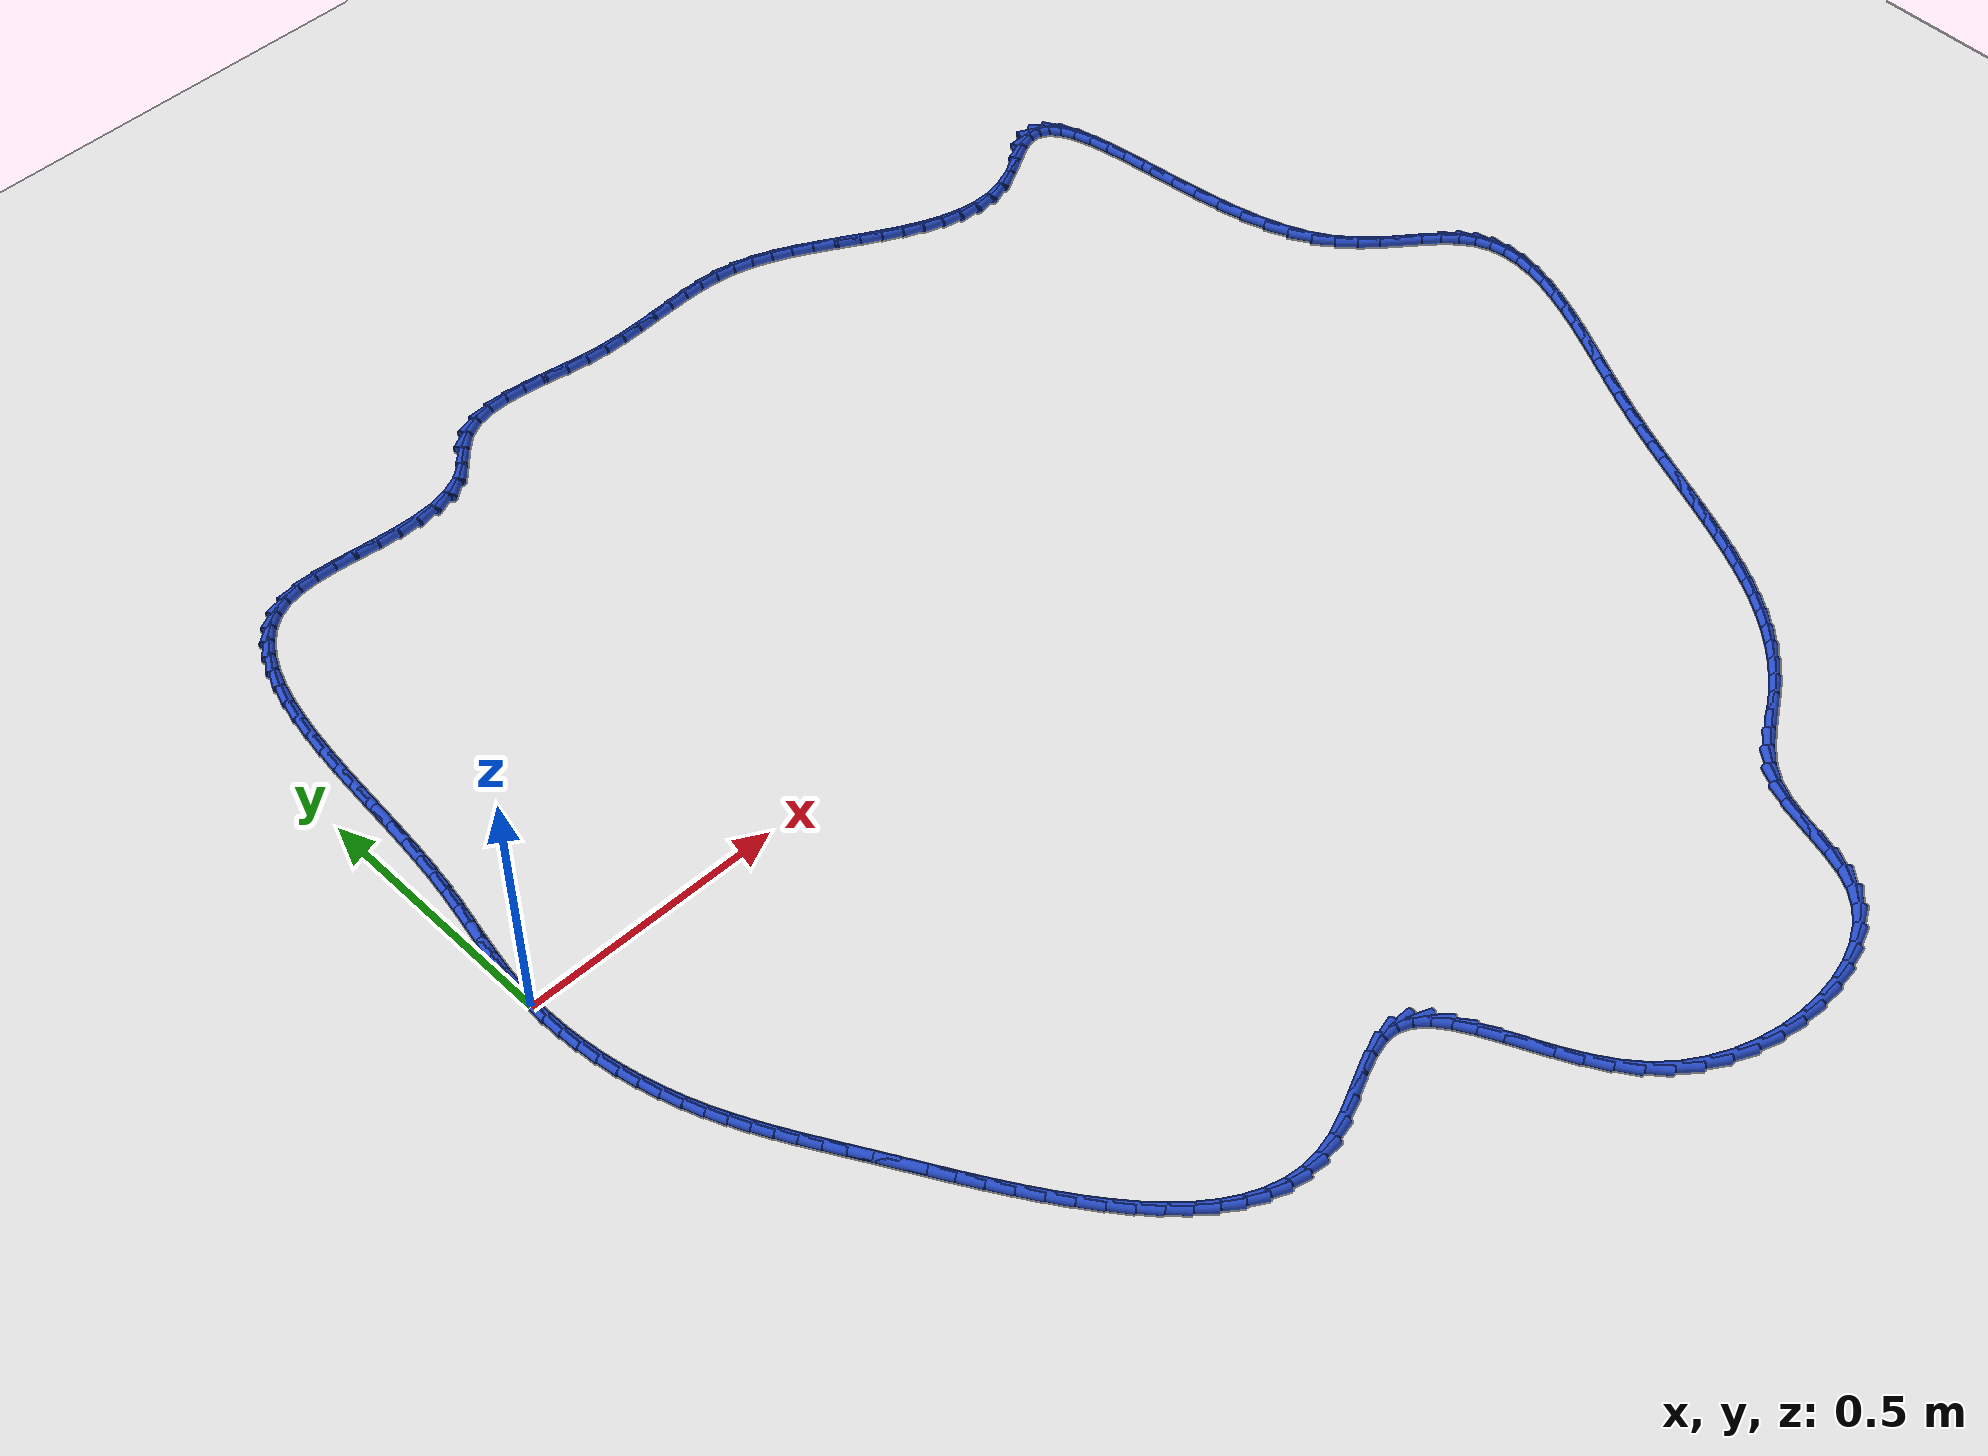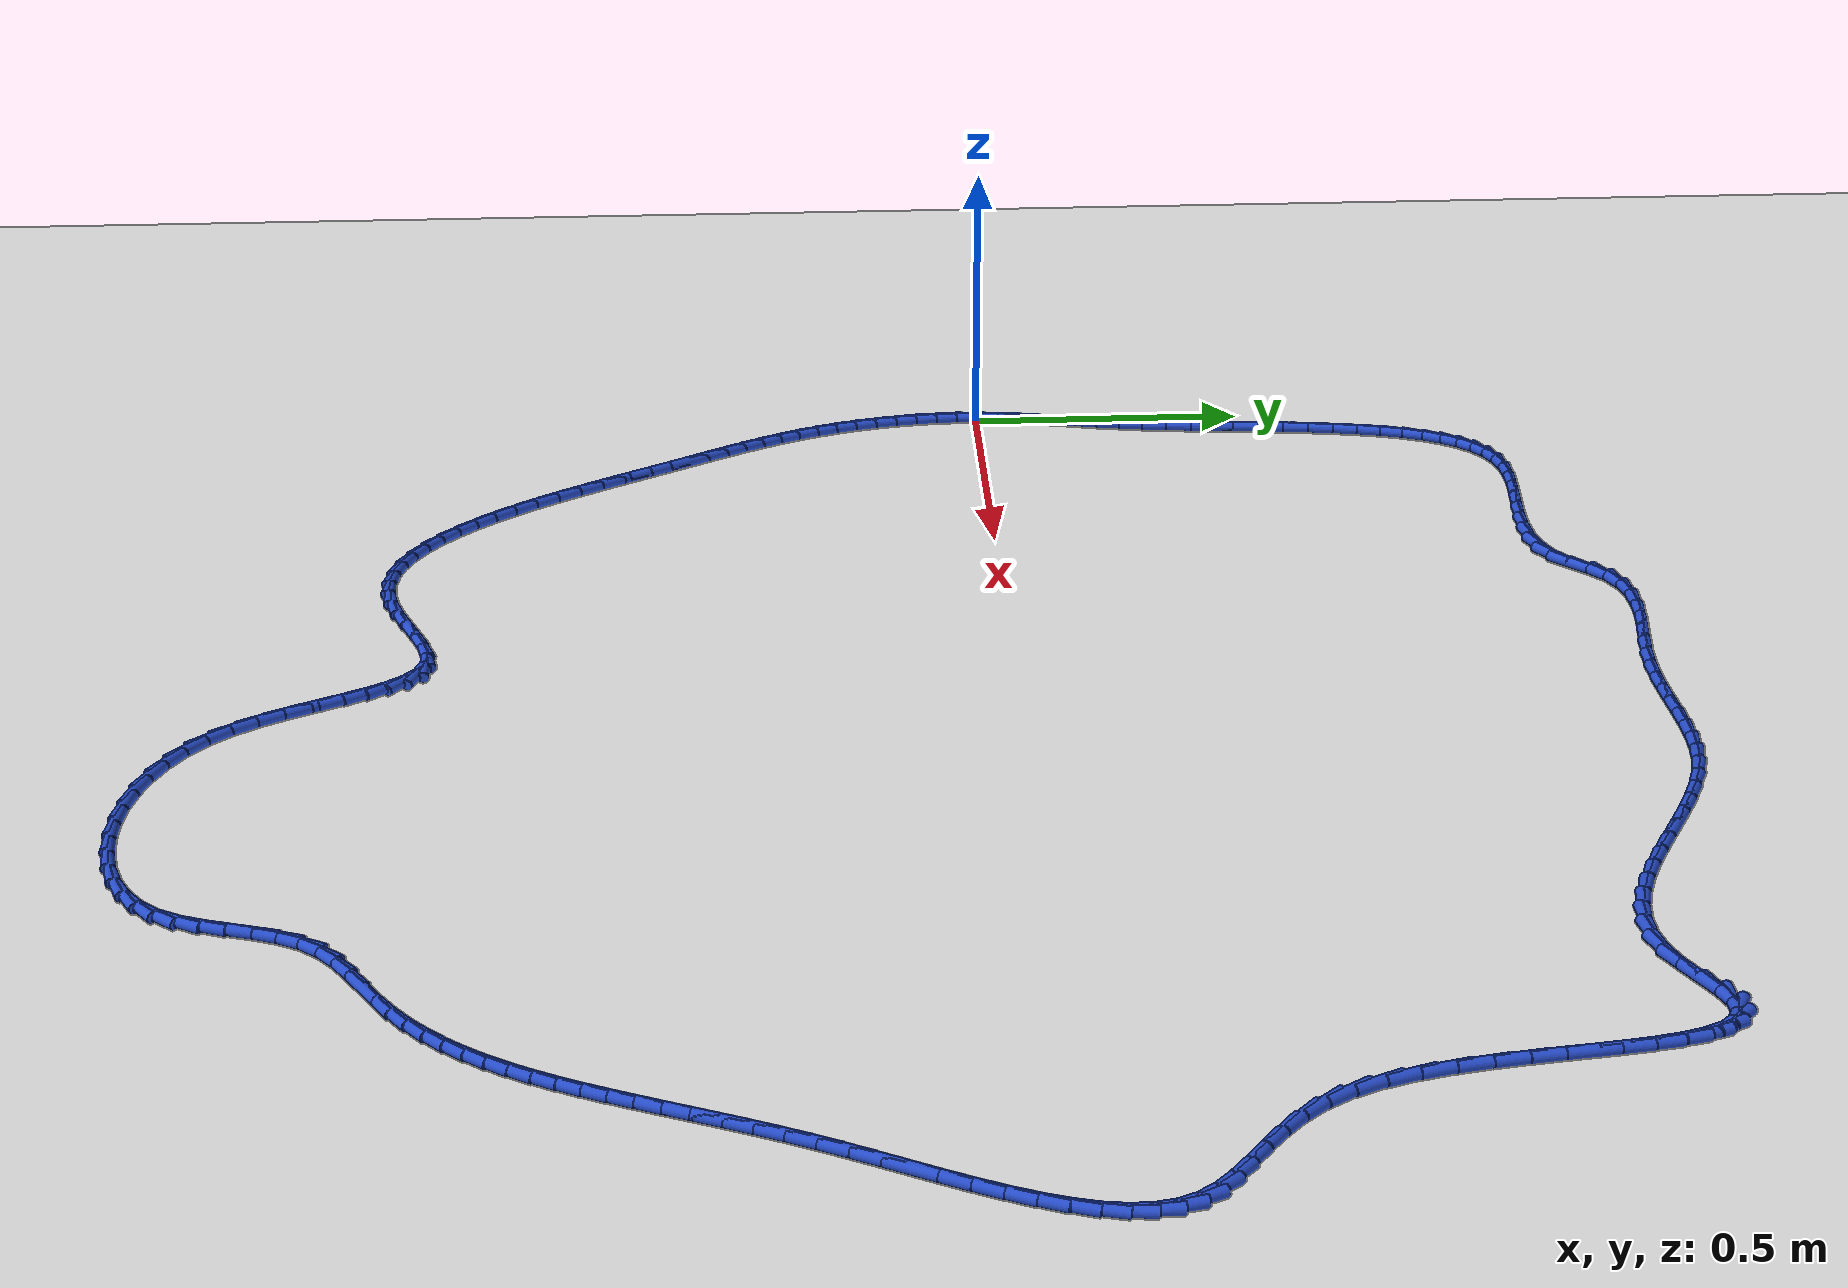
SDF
<sdf version="1.6">
 <world name="default">
  <light name="sun" type="directional">
   <pose>0 0 10 0 -0 0</pose>
   <diffuse>0.8 0.8 0.8 1</diffuse>
   <specular>0.2 0.2 0.2 1</specular>
   <attenuation>
    <range>1000</range>
    <constant>0.9</constant>
    <linear>0.01</linear>
    <quadratic>0.001</quadratic>
   </attenuation>
   <direction>-0.5 0.1 -0.9</direction>
  </light>
  <model name="ground_plane">
   <static>1</static>
   <link name="link">
    <collision name="collision">
     <geometry><plane><normal>0 0 1</normal><size>100 100</size></plane></geometry>
     <surface><friction><ode><mu>100</mu><mu2>50</mu2></ode></friction></surface>
    </collision>
    <visual name="visual">
     <cast_shadows>0</cast_shadows>
     <geometry><plane><normal>0 0 1</normal><size>100 100</size></plane></geometry>
     <material>
      <script><uri>file://media/materials/scripts/gazebo.material</uri><name>Gazebo/WhiteGlow</name></script>
     </material>
    </visual>
   </link>
  </model>
  <gravity>0 0 -9.8</gravity>
  <magnetic_field>6e-06 2.3e-05 -4.2e-05</magnetic_field>
  <atmosphere type="adiabatic"/>
  <physics name="default_physics" default="0" type="ode">
   <max_step_size>0.001</max_step_size>
   <real_time_factor>1</real_time_factor>
   <real_time_update_rate>1000</real_time_update_rate>
  </physics>
  <scene><ambient>0.4 0.4 0.4 1</ambient><background>0.7 0.7 0.7 1</background><shadows>1</shadows></scene>
  <spherical_coordinates>
   <surface_model>EARTH_WGS84</surface_model>
   <latitude_deg>0</latitude_deg>
   <longitude_deg>0</longitude_deg>
   <elevation>0</elevation>
   <heading_deg>0</heading_deg>
  </spherical_coordinates>
  <model name="line">
   <link name="link_0">
    <pose>1.5612511283791264e-17 6.245004513516506e-17 0.01 0 1.57 1.4965390491002946</pose>
    <collision name="collision">
     <geometry><cylinder><radius>0.01</radius><length>0.08</length></cylinder></geometry>
    </collision>
    <visual name="visual">
     <material>
      <script><name>Gazebo/Blue</name><uri>file://media/materials/scripts/gazebo.material</uri></script>
     </material>
     <geometry><cylinder><radius>0.01</radius><length>0.08</length></cylinder></geometry>
    </visual>
   </link>
   <link name="link_1">
    <pose>0.0028098821377485947 0.037770244582822875 0.01 0 1.57 1.4478813549803822</pose>
    <collision name="collision">
     <geometry><cylinder><radius>0.01</radius><length>0.08</length></cylinder></geometry>
    </collision>
    <visual name="visual">
     <material>
      <script><name>Gazebo/Blue</name><uri>file://media/materials/scripts/gazebo.material</uri></script>
     </material>
     <geometry><cylinder><radius>0.01</radius><length>0.08</length></cylinder></geometry>
    </visual>
   </link>
   <link name="link_2">
    <pose>0.007415832168220956 0.07505399336716743 0.01 0 1.57 1.4113431468086133</pose>
    <collision name="collision">
     <geometry><cylinder><radius>0.01</radius><length>0.08</length></cylinder></geometry>
    </collision>
    <visual name="visual">
     <material>
      <script><name>Gazebo/Blue</name><uri>file://media/materials/scripts/gazebo.material</uri></script>
     </material>
     <geometry><cylinder><radius>0.01</radius><length>0.08</length></cylinder></geometry>
    </visual>
   </link>
   <link name="link_3">
    <pose>0.013392882435788308 0.1122204397472849 0.01 0 1.57 1.3878441354074638</pose>
    <collision name="collision">
     <geometry><cylinder><radius>0.01</radius><length>0.08</length></cylinder></geometry>
    </collision>
    <visual name="visual">
     <material>
      <script><name>Gazebo/Blue</name><uri>file://media/materials/scripts/gazebo.material</uri></script>
     </material>
     <geometry><cylinder><radius>0.01</radius><length>0.08</length></cylinder></geometry>
    </visual>
   </link>
   <link name="link_4">
    <pose>0.020316065284821876 0.1496387771174266 0.01 0 1.57 1.3775379466092406</pose>
    <collision name="collision">
     <geometry><cylinder><radius>0.01</radius><length>0.08</length></cylinder></geometry>
    </collision>
    <visual name="visual">
     <material>
      <script><name>Gazebo/Blue</name><uri>file://media/materials/scripts/gazebo.material</uri></script>
     </material>
     <geometry><cylinder><radius>0.01</radius><length>0.08</length></cylinder></geometry>
    </visual>
   </link>
   <link name="link_5">
    <pose>0.02776041305969285 0.18767819887184367 0.01 0 1.57 1.3799475211835062</pose>
    <collision name="collision">
     <geometry><cylinder><radius>0.01</radius><length>0.08</length></cylinder></geometry>
    </collision>
    <visual name="visual">
     <material>
      <script><name>Gazebo/Blue</name><uri>file://media/materials/scripts/gazebo.material</uri></script>
     </material>
     <geometry><cylinder><radius>0.01</radius><length>0.08</length></cylinder></geometry>
    </visual>
   </link>
   <link name="link_6">
    <pose>0.03530095810477245 0.2267078984047874 0.01 0 1.57 1.3941013213438622</pose>
    <collision name="collision">
     <geometry><cylinder><radius>0.01</radius><length>0.08</length></cylinder></geometry>
    </collision>
    <visual name="visual">
     <material>
      <script><name>Gazebo/Blue</name><uri>file://media/materials/scripts/gazebo.material</uri></script>
     </material>
     <geometry><cylinder><radius>0.01</radius><length>0.08</length></cylinder></geometry>
    </visual>
   </link>
   <link name="link_7">
    <pose>0.04251273276443188 0.267097069110509 0.01 0 1.57 1.4186487297515342</pose>
    <collision name="collision">
     <geometry><cylinder><radius>0.01</radius><length>0.08</length></cylinder></geometry>
    </collision>
    <visual name="visual">
     <material>
      <script><name>Gazebo/Blue</name><uri>file://media/materials/scripts/gazebo.material</uri></script>
     </material>
     <geometry><cylinder><radius>0.01</radius><length>0.08</length></cylinder></geometry>
    </visual>
   </link>
   <link name="link_8">
    <pose>0.048970769394922814 0.3092149043697018 0.01 0 1.57 1.4487984110381387</pose>
    <collision name="collision">
     <geometry><cylinder><radius>0.01</radius><length>0.08</length></cylinder></geometry>
    </collision>
    <visual name="visual">
     <material>
      <script><name>Gazebo/Blue</name><uri>file://media/materials/scripts/gazebo.material</uri></script>
     </material>
     <geometry><cylinder><radius>0.01</radius><length>0.08</length></cylinder></geometry>
    </visual>
   </link>
   <link name="link_9">
    <pose>0.05437450703567692 0.35328862596884286 0.01 0 1.57 1.47177717067165</pose>
    <collision name="collision">
     <geometry><cylinder><radius>0.01</radius><length>0.08</length></cylinder></geometry>
    </collision>
    <visual name="visual">
     <material>
      <script><name>Gazebo/Blue</name><uri>file://media/materials/scripts/gazebo.material</uri></script>
     </material>
     <geometry><cylinder><radius>0.01</radius><length>0.08</length></cylinder></geometry>
    </visual>
   </link>
   <link name="link_10">
    <pose>0.05891420357451561 0.39898533840331074 0.01 0 1.57 1.4858984247100178</pose>
    <collision name="collision">
     <geometry><cylinder><radius>0.01</radius><length>0.08</length></cylinder></geometry>
    </collision>
    <visual name="visual">
     <material>
      <script><name>Gazebo/Blue</name><uri>file://media/materials/scripts/gazebo.material</uri></script>
     </material>
     <geometry><cylinder><radius>0.01</radius><length>0.08</length></cylinder></geometry>
    </visual>
   </link>
   <link name="link_11">
    <pose>0.06290114286067174 0.44583403261827953 0.01 0 1.57 1.4921561440001427</pose>
    <collision name="collision">
     <geometry><cylinder><radius>0.01</radius><length>0.08</length></cylinder></geometry>
    </collision>
    <visual name="visual">
     <material>
      <script><name>Gazebo/Blue</name><uri>file://media/materials/scripts/gazebo.material</uri></script>
     </material>
     <geometry><cylinder><radius>0.01</radius><length>0.08</length></cylinder></geometry>
    </visual>
   </link>
   <link name="link_12">
    <pose>0.06664660874337813 0.4933636995589232 0.01 0 1.57 1.4910473928540988</pose>
    <collision name="collision">
     <geometry><cylinder><radius>0.01</radius><length>0.08</length></cylinder></geometry>
    </collision>
    <visual name="visual">
     <material>
      <script><name>Gazebo/Blue</name><uri>file://media/materials/scripts/gazebo.material</uri></script>
     </material>
     <geometry><cylinder><radius>0.01</radius><length>0.08</length></cylinder></geometry>
    </visual>
   </link>
   <link name="link_13">
    <pose>0.0704618850718677 0.5411033301704159 0.01 0 1.57 1.4826409101869793</pose>
    <collision name="collision">
     <geometry><cylinder><radius>0.01</radius><length>0.08</length></cylinder></geometry>
    </collision>
    <visual name="visual">
     <material>
      <script><name>Gazebo/Blue</name><uri>file://media/materials/scripts/gazebo.material</uri></script>
     </material>
     <geometry><cylinder><radius>0.01</radius><length>0.08</length></cylinder></geometry>
    </visual>
   </link>
   <link name="link_14">
    <pose>0.07465825569537324 0.5885819153979318 0.01 0 1.57 1.46659517966814</pose>
    <collision name="collision">
     <geometry><cylinder><radius>0.01</radius><length>0.08</length></cylinder></geometry>
    </collision>
    <visual name="visual">
     <material>
      <script><name>Gazebo/Blue</name><uri>file://media/materials/scripts/gazebo.material</uri></script>
     </material>
     <geometry><cylinder><radius>0.01</radius><length>0.08</length></cylinder></geometry>
    </visual>
   </link>
   <link name="link_15">
    <pose>0.07954700446312765 0.6353284461866449 0.01 0 1.57 1.4421311327295279</pose>
    <collision name="collision">
     <geometry><cylinder><radius>0.01</radius><length>0.08</length></cylinder></geometry>
    </collision>
    <visual name="visual">
     <material>
      <script><name>Gazebo/Blue</name><uri>file://media/materials/scripts/gazebo.material</uri></script>
     </material>
     <geometry><cylinder><radius>0.01</radius><length>0.08</length></cylinder></geometry>
    </visual>
   </link>
   <link name="link_16">
    <pose>0.08543941522436377 0.6808719134817292 0.01 0 1.57 1.4079597764265983</pose>
    <collision name="collision">
     <geometry><cylinder><radius>0.01</radius><length>0.08</length></cylinder></geometry>
    </collision>
    <visual name="visual">
     <material>
      <script><name>Gazebo/Blue</name><uri>file://media/materials/scripts/gazebo.material</uri></script>
     </material>
     <geometry><cylinder><radius>0.01</radius><length>0.08</length></cylinder></geometry>
    </visual>
   </link>
   <link name="link_17">
    <pose>0.09264677182831442 0.7247413082283588 0.01 0 1.57 1.3621638959719053</pose>
    <collision name="collision">
     <geometry><cylinder><radius>0.01</radius><length>0.08</length></cylinder></geometry>
    </collision>
    <visual name="visual">
     <material>
      <script><name>Gazebo/Blue</name><uri>file://media/materials/scripts/gazebo.material</uri></script>
     </material>
     <geometry><cylinder><radius>0.01</radius><length>0.08</length></cylinder></geometry>
    </visual>
   </link>
   <link name="link_18">
    <pose>0.1014803581242125 0.7664656213717077 0.01 0 1.57 1.3020417501642993</pose>
    <collision name="collision">
     <geometry><cylinder><radius>0.01</radius><length>0.08</length></cylinder></geometry>
    </collision>
    <visual name="visual">
     <material>
      <script><name>Gazebo/Blue</name><uri>file://media/materials/scripts/gazebo.material</uri></script>
     </material>
     <geometry><cylinder><radius>0.01</radius><length>0.08</length></cylinder></geometry>
    </visual>
   </link>
   <link name="link_19">
    <pose>0.11225145796129088 0.8055738438569505 0.01 0 1.57 1.2239561674179427</pose>
    <collision name="collision">
     <geometry><cylinder><radius>0.01</radius><length>0.08</length></cylinder></geometry>
    </collision>
    <visual name="visual">
     <material>
      <script><name>Gazebo/Blue</name><uri>file://media/materials/scripts/gazebo.material</uri></script>
     </material>
     <geometry><cylinder><radius>0.01</radius><length>0.08</length></cylinder></geometry>
    </visual>
   </link>
   <link name="link_20">
    <pose>0.12527135518878235 0.8415949666292606 0.01 0 1.57 1.1233331412053595</pose>
    <collision name="collision">
     <geometry><cylinder><radius>0.01</radius><length>0.08</length></cylinder></geometry>
    </collision>
    <visual name="visual">
     <material>
      <script><name>Gazebo/Blue</name><uri>file://media/materials/scripts/gazebo.material</uri></script>
     </material>
     <geometry><cylinder><radius>0.01</radius><length>0.08</length></cylinder></geometry>
    </visual>
   </link>
   <link name="link_21">
    <pose>0.1408513336559198 0.8740579806338125 0.01 0 1.57 0.9951802214433075</pose>
    <collision name="collision">
     <geometry><cylinder><radius>0.01</radius><length>0.08</length></cylinder></geometry>
    </collision>
    <visual name="visual">
     <material>
      <script><name>Gazebo/Blue</name><uri>file://media/materials/scripts/gazebo.material</uri></script>
     </material>
     <geometry><cylinder><radius>0.01</radius><length>0.08</length></cylinder></geometry>
    </visual>
   </link>
   <link name="link_22">
    <pose>0.15930267721193614 0.9024918768157799 0.01 0 1.57 0.8358247603251658</pose>
    <collision name="collision">
     <geometry><cylinder><radius>0.01</radius><length>0.08</length></cylinder></geometry>
    </collision>
    <visual name="visual">
     <material>
      <script><name>Gazebo/Blue</name><uri>file://media/materials/scripts/gazebo.material</uri></script>
     </material>
     <geometry><cylinder><radius>0.01</radius><length>0.08</length></cylinder></geometry>
    </visual>
   </link>
   <link name="link_23">
    <pose>0.18093666970606417 0.9264256461203375 0.01 0 1.57 0.6464665310243447</pose>
    <collision name="collision">
     <geometry><cylinder><radius>0.01</radius><length>0.08</length></cylinder></geometry>
    </collision>
    <visual name="visual">
     <material>
      <script><name>Gazebo/Blue</name><uri>file://media/materials/scripts/gazebo.material</uri></script>
     </material>
     <geometry><cylinder><radius>0.01</radius><length>0.08</length></cylinder></geometry>
    </visual>
   </link>
   <link name="link_24">
    <pose>0.20606459498753663 0.9453882794926585 0.01 0 1.57 0.43714799070508614</pose>
    <collision name="collision">
     <geometry><cylinder><radius>0.01</radius><length>0.08</length></cylinder></geometry>
    </collision>
    <visual name="visual">
     <material>
      <script><name>Gazebo/Blue</name><uri>file://media/materials/scripts/gazebo.material</uri></script>
     </material>
     <geometry><cylinder><radius>0.01</radius><length>0.08</length></cylinder></geometry>
    </visual>
   </link>
   <link name="link_25">
    <pose>0.23499773690558656 0.9589087678779178 0.01 0 1.57 0.22762469775456456</pose>
    <collision name="collision">
     <geometry><cylinder><radius>0.01</radius><length>0.08</length></cylinder></geometry>
    </collision>
    <visual name="visual">
     <material>
      <script><name>Gazebo/Blue</name><uri>file://media/materials/scripts/gazebo.material</uri></script>
     </material>
     <geometry><cylinder><radius>0.01</radius><length>0.08</length></cylinder></geometry>
    </visual>
   </link>
   <link name="link_26">
    <pose>0.26802168174091184 0.9665584089199662 0.01 0 1.57 0.06284638136740443</pose>
    <collision name="collision">
     <geometry><cylinder><radius>0.01</radius><length>0.08</length></cylinder></geometry>
    </collision>
    <visual name="visual">
     <material>
      <script><name>Gazebo/Blue</name><uri>file://media/materials/scripts/gazebo.material</uri></script>
     </material>
     <geometry><cylinder><radius>0.01</radius><length>0.08</length></cylinder></geometry>
    </visual>
   </link>
   <link name="link_27">
    <pose>0.3048349291350598 0.9688750390815352 0.01 0 1.57 -0.03814257007176209</pose>
    <collision name="collision">
     <geometry><cylinder><radius>0.01</radius><length>0.08</length></cylinder></geometry>
    </collision>
    <visual name="visual">
     <material>
      <script><name>Gazebo/Blue</name><uri>file://media/materials/scripts/gazebo.material</uri></script>
     </material>
     <geometry><cylinder><radius>0.01</radius><length>0.08</length></cylinder></geometry>
    </visual>
   </link>
   <link name="link_28">
    <pose>0.3445510822863838 0.9673594278571638 0.01 0 1.57 -0.09099078883400784</pose>
    <collision name="collision">
     <geometry><cylinder><radius>0.01</radius><length>0.08</length></cylinder></geometry>
    </collision>
    <visual name="visual">
     <material>
      <script><name>Gazebo/Blue</name><uri>file://media/materials/scripts/gazebo.material</uri></script>
     </material>
     <geometry><cylinder><radius>0.01</radius><length>0.08</length></cylinder></geometry>
    </visual>
   </link>
   <link name="link_29">
    <pose>0.38625848486581205 0.9635539302794967 0.01 0 1.57 -0.1060125717412685</pose>
    <collision name="collision">
     <geometry><cylinder><radius>0.01</radius><length>0.08</length></cylinder></geometry>
    </collision>
    <visual name="visual">
     <material>
      <script><name>Gazebo/Blue</name><uri>file://media/materials/scripts/gazebo.material</uri></script>
     </material>
     <geometry><cylinder><radius>0.01</radius><length>0.08</length></cylinder></geometry>
    </visual>
   </link>
   <link name="link_30">
    <pose>0.42904548054427294 0.959000901381178 0.01 0 1.57 -0.08726959436672126</pose>
    <collision name="collision">
     <geometry><cylinder><radius>0.01</radius><length>0.08</length></cylinder></geometry>
    </collision>
    <visual name="visual">
     <material>
      <script><name>Gazebo/Blue</name><uri>file://media/materials/scripts/gazebo.material</uri></script>
     </material>
     <geometry><cylinder><radius>0.01</radius><length>0.08</length></cylinder></geometry>
    </visual>
   </link>
   <link name="link_31">
    <pose>0.4720004129926945 0.955242696194853 0.01 0 1.57 -0.0336519585227161</pose>
    <collision name="collision">
     <geometry><cylinder><radius>0.01</radius><length>0.08</length></cylinder></geometry>
    </collision>
    <visual name="visual">
     <material>
      <script><name>Gazebo/Blue</name><uri>file://media/materials/scripts/gazebo.material</uri></script>
     </material>
     <geometry><cylinder><radius>0.01</radius><length>0.08</length></cylinder></geometry>
    </visual>
   </link>
   <link name="link_32">
    <pose>0.5142116258820052 0.9538216697531656 0.01 0 1.57 0.06054621515569539</pose>
    <collision name="collision">
     <geometry><cylinder><radius>0.01</radius><length>0.08</length></cylinder></geometry>
    </collision>
    <visual name="visual">
     <material>
      <script><name>Gazebo/Blue</name><uri>file://media/materials/scripts/gazebo.material</uri></script>
     </material>
     <geometry><cylinder><radius>0.01</radius><length>0.08</length></cylinder></geometry>
    </visual>
   </link>
   <link name="link_33">
    <pose>0.5547674628831326 0.9562801770887599 0.01 0 1.57 0.20453902527993625</pose>
    <collision name="collision">
     <geometry><cylinder><radius>0.01</radius><length>0.08</length></cylinder></geometry>
    </collision>
    <visual name="visual">
     <material>
      <script><name>Gazebo/Blue</name><uri>file://media/materials/scripts/gazebo.material</uri></script>
     </material>
     <geometry><cylinder><radius>0.01</radius><length>0.08</length></cylinder></geometry>
    </visual>
   </link>
   <link name="link_34">
    <pose>0.5927562676670054 0.9641605732342813 0.01 0 1.57 0.4062274194706462</pose>
    <collision name="collision">
     <geometry><cylinder><radius>0.01</radius><length>0.08</length></cylinder></geometry>
    </collision>
    <visual name="visual">
     <material>
      <script><name>Gazebo/Blue</name><uri>file://media/materials/scripts/gazebo.material</uri></script>
     </material>
     <geometry><cylinder><radius>0.01</radius><length>0.08</length></cylinder></geometry>
    </visual>
   </link>
   <link name="link_35">
    <pose>0.6272663839045518 0.9790052132223739 0.01 0 1.57 0.6578633749273951</pose>
    <collision name="collision">
     <geometry><cylinder><radius>0.01</radius><length>0.08</length></cylinder></geometry>
    </collision>
    <visual name="visual">
     <material>
      <script><name>Gazebo/Blue</name><uri>file://media/materials/scripts/gazebo.material</uri></script>
     </material>
     <geometry><cylinder><radius>0.01</radius><length>0.08</length></cylinder></geometry>
    </visual>
   </link>
   <link name="link_36">
    <pose>0.6574138727485572 1.0022997852741065 0.01 0 1.57 0.8253862525907413</pose>
    <collision name="collision">
     <geometry><cylinder><radius>0.01</radius><length>0.08</length></cylinder></geometry>
    </collision>
    <visual name="visual">
     <material>
      <script><name>Gazebo/Blue</name><uri>file://media/materials/scripts/gazebo.material</uri></script>
     </material>
     <geometry><cylinder><radius>0.01</radius><length>0.08</length></cylinder></geometry>
    </visual>
   </link>
   <link name="link_37">
    <pose>0.6843141848363187 1.0314423397881645 0.01 0 1.57 0.7411923184719813</pose>
    <collision name="collision">
     <geometry><cylinder><radius>0.01</radius><length>0.08</length></cylinder></geometry>
    </collision>
    <visual name="visual">
     <material>
      <script><name>Gazebo/Blue</name><uri>file://media/materials/scripts/gazebo.material</uri></script>
     </material>
     <geometry><cylinder><radius>0.01</radius><length>0.08</length></cylinder></geometry>
    </visual>
   </link>
   <link name="link_38">
    <pose>0.7123673513474473 1.0571187946323337 0.01 0 1.57 0.4728027053657131</pose>
    <collision name="collision">
     <geometry><cylinder><radius>0.01</radius><length>0.08</length></cylinder></geometry>
    </collision>
    <visual name="visual">
     <material>
      <script><name>Gazebo/Blue</name><uri>file://media/materials/scripts/gazebo.material</uri></script>
     </material>
     <geometry><cylinder><radius>0.01</radius><length>0.08</length></cylinder></geometry>
    </visual>
   </link>
   <link name="link_39">
    <pose>0.7443828003029087 1.0734945949288803 0.01 0 1.57 0.22557276805663648</pose>
    <collision name="collision">
     <geometry><cylinder><radius>0.01</radius><length>0.08</length></cylinder></geometry>
    </collision>
    <visual name="visual">
     <material>
      <script><name>Gazebo/Blue</name><uri>file://media/materials/scripts/gazebo.material</uri></script>
     </material>
     <geometry><cylinder><radius>0.01</radius><length>0.08</length></cylinder></geometry>
    </visual>
   </link>
   <link name="link_40">
    <pose>0.7799697166015482 1.0816610171792371 0.01 0 1.57 0.04451069179883939</pose>
    <collision name="collision">
     <geometry><cylinder><radius>0.01</radius><length>0.08</length></cylinder></geometry>
    </collision>
    <visual name="visual">
     <material>
      <script><name>Gazebo/Blue</name><uri>file://media/materials/scripts/gazebo.material</uri></script>
     </material>
     <geometry><cylinder><radius>0.01</radius><length>0.08</length></cylinder></geometry>
    </visual>
   </link>
   <link name="link_41">
    <pose>0.8184301399083151 1.0833740486639005 0.01 0 1.57 -0.0733100187703516</pose>
    <collision name="collision">
     <geometry><cylinder><radius>0.01</radius><length>0.08</length></cylinder></geometry>
    </collision>
    <visual name="visual">
     <material>
      <script><name>Gazebo/Blue</name><uri>file://media/materials/scripts/gazebo.material</uri></script>
     </material>
     <geometry><cylinder><radius>0.01</radius><length>0.08</length></cylinder></geometry>
    </visual>
   </link>
   <link name="link_42">
    <pose>0.8590661098881578 1.0803896766633683 0.01 0 1.57 -0.1397919850723292</pose>
    <collision name="collision">
     <geometry><cylinder><radius>0.01</radius><length>0.08</length></cylinder></geometry>
    </collision>
    <visual name="visual">
     <material>
      <script><name>Gazebo/Blue</name><uri>file://media/materials/scripts/gazebo.material</uri></script>
     </material>
     <geometry><cylinder><radius>0.01</radius><length>0.08</length></cylinder></geometry>
    </visual>
   </link>
   <link name="link_43">
    <pose>0.9011796662060252 1.0744638884581361 0.01 0 1.57 -0.16429459482061196</pose>
    <collision name="collision">
     <geometry><cylinder><radius>0.01</radius><length>0.08</length></cylinder></geometry>
    </collision>
    <visual name="visual">
     <material>
      <script><name>Gazebo/Blue</name><uri>file://media/materials/scripts/gazebo.material</uri></script>
     </material>
     <geometry><cylinder><radius>0.01</radius><length>0.08</length></cylinder></geometry>
    </visual>
   </link>
   <link name="link_44">
    <pose>0.9440728485268661 1.0673526713287007 0.01 0 1.57 -0.15103826738000775</pose>
    <collision name="collision">
     <geometry><cylinder><radius>0.01</radius><length>0.08</length></cylinder></geometry>
    </collision>
    <visual name="visual">
     <material>
      <script><name>Gazebo/Blue</name><uri>file://media/materials/scripts/gazebo.material</uri></script>
     </material>
     <geometry><cylinder><radius>0.01</radius><length>0.08</length></cylinder></geometry>
    </visual>
   </link>
   <link name="link_45">
    <pose>0.9870476965156283 1.0608120125555582 0.01 0 1.57 -0.09972917546945442</pose>
    <collision name="collision">
     <geometry><cylinder><radius>0.01</radius><length>0.08</length></cylinder></geometry>
    </collision>
    <visual name="visual">
     <material>
      <script><name>Gazebo/Blue</name><uri>file://media/materials/scripts/gazebo.material</uri></script>
     </material>
     <geometry><cylinder><radius>0.01</radius><length>0.08</length></cylinder></geometry>
    </visual>
   </link>
   <link name="link_46">
    <pose>1.0294138465805753 1.0565728077665497 0.01 0 1.57 -0.031086332727911035</pose>
    <collision name="collision">
     <geometry><cylinder><radius>0.01</radius><length>0.08</length></cylinder></geometry>
    </collision>
    <visual name="visual">
     <material>
      <script><name>Gazebo/Blue</name><uri>file://media/materials/scripts/gazebo.material</uri></script>
     </material>
     <geometry><cylinder><radius>0.01</radius><length>0.08</length></cylinder></geometry>
    </visual>
   </link>
   <link name="link_47">
    <pose>1.0708080224515049 1.055285599980306 0.01 0 1.57 0.020933868234990147</pose>
    <collision name="collision">
     <geometry><cylinder><radius>0.01</radius><length>0.08</length></cylinder></geometry>
    </collision>
    <visual name="visual">
     <material>
      <script><name>Gazebo/Blue</name><uri>file://media/materials/scripts/gazebo.material</uri></script>
     </material>
     <geometry><cylinder><radius>0.01</radius><length>0.08</length></cylinder></geometry>
    </visual>
   </link>
   <link name="link_48">
    <pose>1.11131119343783 1.0561336119023135 0.01 0 1.57 0.05185267464040737</pose>
    <collision name="collision">
     <geometry><cylinder><radius>0.01</radius><length>0.08</length></cylinder></geometry>
    </collision>
    <visual name="visual">
     <material>
      <script><name>Gazebo/Blue</name><uri>file://media/materials/scripts/gazebo.material</uri></script>
     </material>
     <geometry><cylinder><radius>0.01</radius><length>0.08</length></cylinder></geometry>
    </visual>
   </link>
   <link name="link_49">
    <pose>1.151036047870899 1.0581952999391078 0.01 0 1.57 0.060190064966267096</pose>
    <collision name="collision">
     <geometry><cylinder><radius>0.01</radius><length>0.08</length></cylinder></geometry>
    </collision>
    <visual name="visual">
     <material>
      <script><name>Gazebo/Blue</name><uri>file://media/materials/scripts/gazebo.material</uri></script>
     </material>
     <geometry><cylinder><radius>0.01</radius><length>0.08</length></cylinder></geometry>
    </visual>
   </link>
   <link name="link_50">
    <pose>1.1900952740820598 1.060549120497224 0.01 0 1.57 0.04475264383107879</pose>
    <collision name="collision">
     <geometry><cylinder><radius>0.01</radius><length>0.08</length></cylinder></geometry>
    </collision>
    <visual name="visual">
     <material>
      <script><name>Gazebo/Blue</name><uri>file://media/materials/scripts/gazebo.material</uri></script>
     </material>
     <geometry><cylinder><radius>0.01</radius><length>0.08</length></cylinder></geometry>
    </visual>
   </link>
   <link name="link_51">
    <pose>1.2286015604026614 1.0622735299831996 0.01 0 1.57 0.004556650593403881</pose>
    <collision name="collision">
     <geometry><cylinder><radius>0.01</radius><length>0.08</length></cylinder></geometry>
    </collision>
    <visual name="visual">
     <material>
      <script><name>Gazebo/Blue</name><uri>file://media/materials/scripts/gazebo.material</uri></script>
     </material>
     <geometry><cylinder><radius>0.01</radius><length>0.08</length></cylinder></geometry>
    </visual>
   </link>
   <link name="link_52">
    <pose>1.266667595164052 1.0624469848035698 0.01 0 1.57 -0.060845220206124255</pose>
    <collision name="collision">
     <geometry><cylinder><radius>0.01</radius><length>0.08</length></cylinder></geometry>
    </collision>
    <visual name="visual">
     <material>
      <script><name>Gazebo/Blue</name><uri>file://media/materials/scripts/gazebo.material</uri></script>
     </material>
     <geometry><cylinder><radius>0.01</radius><length>0.08</length></cylinder></geometry>
    </visual>
   </link>
   <link name="link_53">
    <pose>1.30440606669758 1.0601479413648711 0.01 0 1.57 -0.1505718089831201</pose>
    <collision name="collision">
     <geometry><cylinder><radius>0.01</radius><length>0.08</length></cylinder></geometry>
    </collision>
    <visual name="visual">
     <material>
      <script><name>Gazebo/Blue</name><uri>file://media/materials/scripts/gazebo.material</uri></script>
     </material>
     <geometry><cylinder><radius>0.01</radius><length>0.08</length></cylinder></geometry>
    </visual>
   </link>
   <link name="link_54">
    <pose>1.3419296633345938 1.0544548560736393 0.01 0 1.57 -0.2596410427195901</pose>
    <collision name="collision">
     <geometry><cylinder><radius>0.01</radius><length>0.08</length></cylinder></geometry>
    </collision>
    <visual name="visual">
     <material>
      <script><name>Gazebo/Blue</name><uri>file://media/materials/scripts/gazebo.material</uri></script>
     </material>
     <geometry><cylinder><radius>0.01</radius><length>0.08</length></cylinder></geometry>
    </visual>
   </link>
   <link name="link_55">
    <pose>1.379347017007223 1.0445154143154243 0.01 0 1.57 -0.3595870499645327</pose>
    <collision name="collision">
     <geometry><cylinder><radius>0.01</radius><length>0.08</length></cylinder></geometry>
    </collision>
    <visual name="visual">
     <material>
      <script><name>Gazebo/Blue</name><uri>file://media/materials/scripts/gazebo.material</uri></script>
     </material>
     <geometry><cylinder><radius>0.01</radius><length>0.08</length></cylinder></geometry>
    </visual>
   </link>
   <link name="link_56">
    <pose>1.4167085922039224 1.03047002248785 0.01 0 1.57 -0.43344471882655145</pose>
    <collision name="collision">
     <geometry><cylinder><radius>0.01</radius><length>0.08</length></cylinder></geometry>
    </collision>
    <visual name="visual">
     <material>
      <script><name>Gazebo/Blue</name><uri>file://media/materials/scripts/gazebo.material</uri></script>
     </material>
     <geometry><cylinder><radius>0.01</radius><length>0.08</length></cylinder></geometry>
    </visual>
   </link>
   <link name="link_57">
    <pose>1.4540213348639976 1.013201801046844 0.01 0 1.57 -0.4839385955201175</pose>
    <collision name="collision">
     <geometry><cylinder><radius>0.01</radius><length>0.08</length></cylinder></geometry>
    </collision>
    <visual name="visual">
     <material>
      <script><name>Gazebo/Blue</name><uri>file://media/materials/scripts/gazebo.material</uri></script>
     </material>
     <geometry><cylinder><radius>0.01</radius><length>0.08</length></cylinder></geometry>
    </visual>
   </link>
   <link name="link_58">
    <pose>1.4912911418374926 0.9936117748444716 0.01 0 1.57 -0.5137630004267688</pose>
    <collision name="collision">
     <geometry><cylinder><radius>0.01</radius><length>0.08</length></cylinder></geometry>
    </collision>
    <visual name="visual">
     <material>
      <script><name>Gazebo/Blue</name><uri>file://media/materials/scripts/gazebo.material</uri></script>
     </material>
     <geometry><cylinder><radius>0.01</radius><length>0.08</length></cylinder></geometry>
    </visual>
   </link>
   <link name="link_59">
    <pose>1.528523909974453 0.972600968732796 0.01 0 1.57 -0.52465035442699</pose>
    <collision name="collision">
     <geometry><cylinder><radius>0.01</radius><length>0.08</length></cylinder></geometry>
    </collision>
    <visual name="visual">
     <material>
      <script><name>Gazebo/Blue</name><uri>file://media/materials/scripts/gazebo.material</uri></script>
     </material>
     <geometry><cylinder><radius>0.01</radius><length>0.08</length></cylinder></geometry>
    </visual>
   </link>
   <link name="link_60">
    <pose>1.565725536124922 0.951070407563882 0.01 0 1.57 -0.5172307353071692</pose>
    <collision name="collision">
     <geometry><cylinder><radius>0.01</radius><length>0.08</length></cylinder></geometry>
    </collision>
    <visual name="visual">
     <material>
      <script><name>Gazebo/Blue</name><uri>file://media/materials/scripts/gazebo.material</uri></script>
     </material>
     <geometry><cylinder><radius>0.01</radius><length>0.08</length></cylinder></geometry>
    </visual>
   </link>
   <link name="link_61">
    <pose>1.6029019171389443 0.9299211161897938 0.01 0 1.57 -0.49100255553708755</pose>
    <collision name="collision">
     <geometry><cylinder><radius>0.01</radius><length>0.08</length></cylinder></geometry>
    </collision>
    <visual name="visual">
     <material>
      <script><name>Gazebo/Blue</name><uri>file://media/materials/scripts/gazebo.material</uri></script>
     </material>
     <geometry><cylinder><radius>0.01</radius><length>0.08</length></cylinder></geometry>
    </visual>
   </link>
   <link name="link_62">
    <pose>1.6400589498665648 0.9100541194625957 0.01 0 1.57 -0.44433707481541196</pose>
    <collision name="collision">
     <geometry><cylinder><radius>0.01</radius><length>0.08</length></cylinder></geometry>
    </collision>
    <visual name="visual">
     <material>
      <script><name>Gazebo/Blue</name><uri>file://media/materials/scripts/gazebo.material</uri></script>
     </material>
     <geometry><cylinder><radius>0.01</radius><length>0.08</length></cylinder></geometry>
    </visual>
   </link>
   <link name="link_63">
    <pose>1.677202531157827 0.8923704422343516 0.01 0 1.57 -0.3745710589164938</pose>
    <collision name="collision">
     <geometry><cylinder><radius>0.01</radius><length>0.08</length></cylinder></geometry>
    </collision>
    <visual name="visual">
     <material>
      <script><name>Gazebo/Blue</name><uri>file://media/materials/scripts/gazebo.material</uri></script>
     </material>
     <geometry><cylinder><radius>0.01</radius><length>0.08</length></cylinder></geometry>
    </visual>
   </link>
   <link name="link_64">
    <pose>1.7143385578627766 0.8777711093571263 0.01 0 1.57 -0.2784028276761741</pose>
    <collision name="collision">
     <geometry><cylinder><radius>0.01</radius><length>0.08</length></cylinder></geometry>
    </collision>
    <visual name="visual">
     <material>
      <script><name>Gazebo/Blue</name><uri>file://media/materials/scripts/gazebo.material</uri></script>
     </material>
     <geometry><cylinder><radius>0.01</radius><length>0.08</length></cylinder></geometry>
    </visual>
   </link>
   <link name="link_65">
    <pose>1.7514729268314564 0.8671571456829839 0.01 0 1.57 -0.15301591674439308</pose>
    <collision name="collision">
     <geometry><cylinder><radius>0.01</radius><length>0.08</length></cylinder></geometry>
    </collision>
    <visual name="visual">
     <material>
      <script><name>Gazebo/Blue</name><uri>file://media/materials/scripts/gazebo.material</uri></script>
     </material>
     <geometry><cylinder><radius>0.01</radius><length>0.08</length></cylinder></geometry>
    </visual>
   </link>
   <link name="link_66">
    <pose>1.7886115349139116 0.8614295760639881 0.01 0 1.57 0.001611070252086605</pose>
    <collision name="collision">
     <geometry><cylinder><radius>0.01</radius><length>0.08</length></cylinder></geometry>
    </collision>
    <visual name="visual">
     <material>
      <script><name>Gazebo/Blue</name><uri>file://media/materials/scripts/gazebo.material</uri></script>
     </material>
     <geometry><cylinder><radius>0.01</radius><length>0.08</length></cylinder></geometry>
    </visual>
   </link>
   <link name="link_67">
    <pose>1.8257602789601868 0.861489425352204 0.01 0 1.57 0.17962066041309616</pose>
    <collision name="collision">
     <geometry><cylinder><radius>0.01</radius><length>0.08</length></cylinder></geometry>
    </collision>
    <visual name="visual">
     <material>
      <script><name>Gazebo/Blue</name><uri>file://media/materials/scripts/gazebo.material</uri></script>
     </material>
     <geometry><cylinder><radius>0.01</radius><length>0.08</length></cylinder></geometry>
    </visual>
   </link>
   <link name="link_68">
    <pose>1.8629250558203254 0.868237718399695 0.01 0 1.57 0.3672955735753101</pose>
    <collision name="collision">
     <geometry><cylinder><radius>0.01</radius><length>0.08</length></cylinder></geometry>
    </collision>
    <visual name="visual">
     <material>
      <script><name>Gazebo/Blue</name><uri>file://media/materials/scripts/gazebo.material</uri></script>
     </material>
     <geometry><cylinder><radius>0.01</radius><length>0.08</length></cylinder></geometry>
    </visual>
   </link>
   <link name="link_69">
    <pose>1.9001036048585975 0.8825423562308676 0.01 0 1.57 0.5007830896402232</pose>
    <collision name="collision">
     <geometry><cylinder><radius>0.01</radius><length>0.08</length></cylinder></geometry>
    </collision>
    <visual name="visual">
     <material>
      <script><name>Gazebo/Blue</name><uri>file://media/materials/scripts/gazebo.material</uri></script>
     </material>
     <geometry><cylinder><radius>0.01</radius><length>0.08</length></cylinder></geometry>
    </visual>
   </link>
   <link name="link_70">
    <pose>1.9366179243236898 0.9025273635249522 0.01 0 1.57 0.5103180121765475</pose>
    <collision name="collision">
     <geometry><cylinder><radius>0.01</radius><length>0.08</length></cylinder></geometry>
    </collision>
    <visual name="visual">
     <material>
      <script><name>Gazebo/Blue</name><uri>file://media/materials/scripts/gazebo.material</uri></script>
     </material>
     <geometry><cylinder><radius>0.01</radius><length>0.08</length></cylinder></geometry>
    </visual>
   </link>
   <link name="link_71">
    <pose>1.970618583604654 0.9215601268583805 0.01 0 1.57 0.3598792361011764</pose>
    <collision name="collision">
     <geometry><cylinder><radius>0.01</radius><length>0.08</length></cylinder></geometry>
    </collision>
    <visual name="visual">
     <material>
      <script><name>Gazebo/Blue</name><uri>file://media/materials/scripts/gazebo.material</uri></script>
     </material>
     <geometry><cylinder><radius>0.01</radius><length>0.08</length></cylinder></geometry>
    </visual>
   </link>
   <link name="link_72">
    <pose>2.0001878892461984 0.9326860211810064 0.01 0 1.57 0.0037300558326342683</pose>
    <collision name="collision">
     <geometry><cylinder><radius>0.01</radius><length>0.08</length></cylinder></geometry>
    </collision>
    <visual name="visual">
     <material>
      <script><name>Gazebo/Blue</name><uri>file://media/materials/scripts/gazebo.material</uri></script>
     </material>
     <geometry><cylinder><radius>0.01</radius><length>0.08</length></cylinder></geometry>
    </visual>
   </link>
   <link name="link_73">
    <pose>2.024628020341558 0.9327771846573448 0.01 0 1.57 -0.4679993530930293</pose>
    <collision name="collision">
     <geometry><cylinder><radius>0.01</radius><length>0.08</length></cylinder></geometry>
    </collision>
    <visual name="visual">
     <material>
      <script><name>Gazebo/Blue</name><uri>file://media/materials/scripts/gazebo.material</uri></script>
     </material>
     <geometry><cylinder><radius>0.01</radius><length>0.08</length></cylinder></geometry>
    </visual>
   </link>
   <link name="link_74">
    <pose>2.044521438283895 0.9227220251971822 0.01 0 1.57 -0.8743917980743511</pose>
    <collision name="collision">
     <geometry><cylinder><radius>0.01</radius><length>0.08</length></cylinder></geometry>
    </collision>
    <visual name="visual">
     <material>
      <script><name>Gazebo/Blue</name><uri>file://media/materials/scripts/gazebo.material</uri></script>
     </material>
     <geometry><cylinder><radius>0.01</radius><length>0.08</length></cylinder></geometry>
    </visual>
   </link>
   <link name="link_75">
    <pose>2.06051123468797 0.9035991488601016 0.01 0 1.57 -1.1318393550662698</pose>
    <collision name="collision">
     <geometry><cylinder><radius>0.01</radius><length>0.08</length></cylinder></geometry>
    </collision>
    <visual name="visual">
     <material>
      <script><name>Gazebo/Blue</name><uri>file://media/materials/scripts/gazebo.material</uri></script>
     </material>
     <geometry><cylinder><radius>0.01</radius><length>0.08</length></cylinder></geometry>
    </visual>
   </link>
   <link name="link_76">
    <pose>2.0732405011685424 0.8764871617056855 0.01 0 1.57 -1.2819010362793966</pose>
    <collision name="collision">
     <geometry><cylinder><radius>0.01</radius><length>0.08</length></cylinder></geometry>
    </collision>
    <visual name="visual">
     <material>
      <script><name>Gazebo/Blue</name><uri>file://media/materials/scripts/gazebo.material</uri></script>
     </material>
     <geometry><cylinder><radius>0.01</radius><length>0.08</length></cylinder></geometry>
    </visual>
   </link>
   <link name="link_77">
    <pose>2.0833523293403733 0.842464669793517 0.01 0 1.57 -1.3693844968952027</pose>
    <collision name="collision">
     <geometry><cylinder><radius>0.01</radius><length>0.08</length></cylinder></geometry>
    </collision>
    <visual name="visual">
     <material>
      <script><name>Gazebo/Blue</name><uri>file://media/materials/scripts/gazebo.material</uri></script>
     </material>
     <geometry><cylinder><radius>0.01</radius><length>0.08</length></cylinder></geometry>
    </visual>
   </link>
   <link name="link_78">
    <pose>2.091489810818226 0.8026102791831793 0.01 0 1.57 -1.4193844165583134</pose>
    <collision name="collision">
     <geometry><cylinder><radius>0.01</radius><length>0.08</length></cylinder></geometry>
    </collision>
    <visual name="visual">
     <material>
      <script><name>Gazebo/Blue</name><uri>file://media/materials/scripts/gazebo.material</uri></script>
     </material>
     <geometry><cylinder><radius>0.01</radius><length>0.08</length></cylinder></geometry>
    </visual>
   </link>
   <link name="link_79">
    <pose>2.098296037216859 0.7580025959342547 0.01 0 1.57 -1.4447538404211673</pose>
    <collision name="collision">
     <geometry><cylinder><radius>0.01</radius><length>0.08</length></cylinder></geometry>
    </collision>
    <visual name="visual">
     <material>
      <script><name>Gazebo/Blue</name><uri>file://media/materials/scripts/gazebo.material</uri></script>
     </material>
     <geometry><cylinder><radius>0.01</radius><length>0.08</length></cylinder></geometry>
    </visual>
   </link>
   <link name="link_80">
    <pose>2.104414100151034 0.7097202261063265 0.01 0 1.57 -1.4519956647999719</pose>
    <collision name="collision">
     <geometry><cylinder><radius>0.01</radius><length>0.08</length></cylinder></geometry>
    </collision>
    <visual name="visual">
     <material>
      <script><name>Gazebo/Blue</name><uri>file://media/materials/scripts/gazebo.material</uri></script>
     </material>
     <geometry><cylinder><radius>0.01</radius><length>0.08</length></cylinder></geometry>
    </visual>
   </link>
   <link name="link_81">
    <pose>2.110487091235512 0.6588417757589773 0.01 0 1.57 -1.4441583998516991</pose>
    <collision name="collision">
     <geometry><cylinder><radius>0.01</radius><length>0.08</length></cylinder></geometry>
    </collision>
    <visual name="visual">
     <material>
      <script><name>Gazebo/Blue</name><uri>file://media/materials/scripts/gazebo.material</uri></script>
     </material>
     <geometry><cylinder><radius>0.01</radius><length>0.08</length></cylinder></geometry>
    </visual>
   </link>
   <link name="link_82">
    <pose>2.1171581020850545 0.6064458509517902 0.01 0 1.57 -1.4221488145944479</pose>
    <collision name="collision">
     <geometry><cylinder><radius>0.01</radius><length>0.08</length></cylinder></geometry>
    </collision>
    <visual name="visual">
     <material>
      <script><name>Gazebo/Blue</name><uri>file://media/materials/scripts/gazebo.material</uri></script>
     </material>
     <geometry><cylinder><radius>0.01</radius><length>0.08</length></cylinder></geometry>
    </visual>
   </link>
   <link name="link_83">
    <pose>2.1250702243144226 0.5536110577443482 0.01 0 1.57 -1.3852678850042155</pose>
    <collision name="collision">
     <geometry><cylinder><radius>0.01</radius><length>0.08</length></cylinder></geometry>
    </collision>
    <visual name="visual">
     <material>
      <script><name>Gazebo/Blue</name><uri>file://media/materials/scripts/gazebo.material</uri></script>
     </material>
     <geometry><cylinder><radius>0.01</radius><length>0.08</length></cylinder></geometry>
    </visual>
   </link>
   <link name="link_84">
    <pose>2.134866549538376 0.5014160021962345 0.01 0 1.57 -1.3313361154118093</pose>
    <collision name="collision">
     <geometry><cylinder><radius>0.01</radius><length>0.08</length></cylinder></geometry>
    </collision>
    <visual name="visual">
     <material>
      <script><name>Gazebo/Blue</name><uri>file://media/materials/scripts/gazebo.material</uri></script>
     </material>
     <geometry><cylinder><radius>0.01</radius><length>0.08</length></cylinder></geometry>
    </visual>
   </link>
   <link name="link_85">
    <pose>2.147190169371676 0.45093929036703095 0.01 0 1.57 -1.2566007854389787</pose>
    <collision name="collision">
     <geometry><cylinder><radius>0.01</radius><length>0.08</length></cylinder></geometry>
    </collision>
    <visual name="visual">
     <material>
      <script><name>Gazebo/Blue</name><uri>file://media/materials/scripts/gazebo.material</uri></script>
     </material>
     <geometry><cylinder><radius>0.01</radius><length>0.08</length></cylinder></geometry>
    </visual>
   </link>
   <link name="link_86">
    <pose>2.162684175429085 0.4032595283163211 0.01 0 1.57 -1.1556463646348278</pose>
    <collision name="collision">
     <geometry><cylinder><radius>0.01</radius><length>0.08</length></cylinder></geometry>
    </collision>
    <visual name="visual">
     <material>
      <script><name>Gazebo/Blue</name><uri>file://media/materials/scripts/gazebo.material</uri></script>
     </material>
     <geometry><cylinder><radius>0.01</radius><length>0.08</length></cylinder></geometry>
    </visual>
   </link>
   <link name="link_87">
    <pose>2.1819916593253623 0.35945532210368775 0.01 0 1.57 -1.0222773114358161</pose>
    <collision name="collision">
     <geometry><cylinder><radius>0.01</radius><length>0.08</length></cylinder></geometry>
    </collision>
    <visual name="visual">
     <material>
      <script><name>Gazebo/Blue</name><uri>file://media/materials/scripts/gazebo.material</uri></script>
     </material>
     <geometry><cylinder><radius>0.01</radius><length>0.08</length></cylinder></geometry>
    </visual>
   </link>
   <link name="link_88">
    <pose>2.2057406587779242 0.3205906688175745 0.01 0 1.57 -0.8783014978356316</pose>
    <collision name="collision">
     <geometry><cylinder><radius>0.01</radius><length>0.08</length></cylinder></geometry>
    </collision>
    <visual name="visual">
     <material>
      <script><name>Gazebo/Blue</name><uri>file://media/materials/scripts/gazebo.material</uri></script>
     </material>
     <geometry><cylinder><radius>0.01</radius><length>0.08</length></cylinder></geometry>
    </visual>
   </link>
   <link name="link_89">
    <pose>2.2336955181028215 0.28689139907802963 0.01 0 1.57 -0.7684052201431383</pose>
    <collision name="collision">
     <geometry><cylinder><radius>0.01</radius><length>0.08</length></cylinder></geometry>
    </collision>
    <visual name="visual">
     <material>
      <script><name>Gazebo/Blue</name><uri>file://media/materials/scripts/gazebo.material</uri></script>
     </material>
     <geometry><cylinder><radius>0.01</radius><length>0.08</length></cylinder></geometry>
    </visual>
   </link>
   <link name="link_90">
    <pose>2.264304110767659 0.257305781675815 0.01 0 1.57 -0.7002813731320996</pose>
    <collision name="collision">
     <geometry><cylinder><radius>0.01</radius><length>0.08</length></cylinder></geometry>
    </collision>
    <visual name="visual">
     <material>
      <script><name>Gazebo/Blue</name><uri>file://media/materials/scripts/gazebo.material</uri></script>
     </material>
     <geometry><cylinder><radius>0.01</radius><length>0.08</length></cylinder></geometry>
    </visual>
   </link>
   <link name="link_91">
    <pose>2.2959036270567736 0.23067467352071325 0.01 0 1.57 -0.6765843417316757</pose>
    <collision name="collision">
     <geometry><cylinder><radius>0.01</radius><length>0.08</length></cylinder></geometry>
    </collision>
    <visual name="visual">
     <material>
      <script><name>Gazebo/Blue</name><uri>file://media/materials/scripts/gazebo.material</uri></script>
     </material>
     <geometry><cylinder><radius>0.01</radius><length>0.08</length></cylinder></geometry>
    </visual>
   </link>
   <link name="link_92">
    <pose>2.3268312572545007 0.20583893152250674 0.01 0 1.57 -0.7023689670823451</pose>
    <collision name="collision">
     <geometry><cylinder><radius>0.01</radius><length>0.08</length></cylinder></geometry>
    </collision>
    <visual name="visual">
     <material>
      <script><name>Gazebo/Blue</name><uri>file://media/materials/scripts/gazebo.material</uri></script>
     </material>
     <geometry><cylinder><radius>0.01</radius><length>0.08</length></cylinder></geometry>
    </visual>
   </link>
   <link name="link_93">
    <pose>2.3554241916451772 0.18163941259097816 0.01 0 1.57 -0.7879734938389487</pose>
    <collision name="collision">
     <geometry><cylinder><radius>0.01</radius><length>0.08</length></cylinder></geometry>
    </collision>
    <visual name="visual">
     <material>
      <script><name>Gazebo/Blue</name><uri>file://media/materials/scripts/gazebo.material</uri></script>
     </material>
     <geometry><cylinder><radius>0.01</radius><length>0.08</length></cylinder></geometry>
    </visual>
   </link>
   <link name="link_94">
    <pose>2.38001962051314 0.15691697363591006 0.01 0 1.57 -0.9486336748854539</pose>
    <collision name="collision">
     <geometry><cylinder><radius>0.01</radius><length>0.08</length></cylinder></geometry>
    </collision>
    <visual name="visual">
     <material>
      <script><name>Gazebo/Blue</name><uri>file://media/materials/scripts/gazebo.material</uri></script>
     </material>
     <geometry><cylinder><radius>0.01</radius><length>0.08</length></cylinder></geometry>
    </visual>
   </link>
   <link name="link_95">
    <pose>2.3989558786714698 0.130513161372158 0.01 0 1.57 -1.1715739580049995</pose>
    <collision name="collision">
     <geometry><cylinder><radius>0.01</radius><length>0.08</length></cylinder></geometry>
    </collision>
    <visual name="visual">
     <material>
      <script><name>Gazebo/Blue</name><uri>file://media/materials/scripts/gazebo.material</uri></script>
     </material>
     <geometry><cylinder><radius>0.01</radius><length>0.08</length></cylinder></geometry>
    </visual>
   </link>
   <link name="link_96">
    <pose>2.411146772119244 0.1016163577910761 0.01 0 1.57 -1.3854615524039875</pose>
    <collision name="collision">
     <geometry><cylinder><radius>0.01</radius><length>0.08</length></cylinder></geometry>
    </collision>
    <visual name="visual">
     <material>
      <script><name>Gazebo/Blue</name><uri>file://media/materials/scripts/gazebo.material</uri></script>
     </material>
     <geometry><cylinder><radius>0.01</radius><length>0.08</length></cylinder></geometry>
    </visual>
   </link>
   <link name="link_97">
    <pose>2.4170137389841084 0.07032359160498998 0.01 0 1.57 -1.56456660841539</pose>
    <collision name="collision">
     <geometry><cylinder><radius>0.01</radius><length>0.08</length></cylinder></geometry>
    </collision>
    <visual name="visual">
     <material>
      <script><name>Gazebo/Blue</name><uri>file://media/materials/scripts/gazebo.material</uri></script>
     </material>
     <geometry><cylinder><radius>0.01</radius><length>0.08</length></cylinder></geometry>
    </visual>
   </link>
   <link name="link_98">
    <pose>2.4172220928467656 0.03687887475014785 0.01 0 1.57 1.4362648897896293</pose>
    <collision name="collision">
     <geometry><cylinder><radius>0.01</radius><length>0.08</length></cylinder></geometry>
    </collision>
    <visual name="visual">
     <material>
      <script><name>Gazebo/Blue</name><uri>file://media/materials/scripts/gazebo.material</uri></script>
     </material>
     <geometry><cylinder><radius>0.01</radius><length>0.08</length></cylinder></geometry>
    </visual>
   </link>
   <link name="link_99">
    <pose>2.4124371472879167 0.0015262191627975607 0.01 0 1.57 1.3294113588540364</pose>
    <collision name="collision">
     <geometry><cylinder><radius>0.01</radius><length>0.08</length></cylinder></geometry>
    </collision>
    <visual name="visual">
     <material>
      <script><name>Gazebo/Blue</name><uri>file://media/materials/scripts/gazebo.material</uri></script>
     </material>
     <geometry><cylinder><radius>0.01</radius><length>0.08</length></cylinder></geometry>
    </visual>
   </link>
   <link name="link_100">
    <pose>2.4033242158882646 -0.03549036322081298 0.01 0 1.57 1.2499021268180304</pose>
    <collision name="collision">
     <geometry><cylinder><radius>0.01</radius><length>0.08</length></cylinder></geometry>
    </collision>
    <visual name="visual">
     <material>
      <script><name>Gazebo/Blue</name><uri>file://media/materials/scripts/gazebo.material</uri></script>
     </material>
     <geometry><cylinder><radius>0.01</radius><length>0.08</length></cylinder></geometry>
    </visual>
   </link>
   <link name="link_101">
    <pose>2.3905486122285096 -0.07392686046443589 0.01 0 1.57 1.1918577890470754</pose>
    <collision name="collision">
     <geometry><cylinder><radius>0.01</radius><length>0.08</length></cylinder></geometry>
    </collision>
    <visual name="visual">
     <material>
      <script><name>Gazebo/Blue</name><uri>file://media/materials/scripts/gazebo.material</uri></script>
     </material>
     <geometry><cylinder><radius>0.01</radius><length>0.08</length></cylinder></geometry>
    </visual>
   </link>
   <link name="link_102">
    <pose>2.3747756498893544 -0.11353926063182336 0.01 0 1.57 1.1508160658562885</pose>
    <collision name="collision">
     <geometry><cylinder><radius>0.01</radius><length>0.08</length></cylinder></geometry>
    </collision>
    <visual name="visual">
     <material>
      <script><name>Gazebo/Blue</name><uri>file://media/materials/scripts/gazebo.material</uri></script>
     </material>
     <geometry><cylinder><radius>0.01</radius><length>0.08</length></cylinder></geometry>
    </visual>
   </link>
   <link name="link_103">
    <pose>2.356670642451502 -0.15408355178672742 0.01 0 1.57 1.1236647926919492</pose>
    <collision name="collision">
     <geometry><cylinder><radius>0.01</radius><length>0.08</length></cylinder></geometry>
    </collision>
    <visual name="visual">
     <material>
      <script><name>Gazebo/Blue</name><uri>file://media/materials/scripts/gazebo.material</uri></script>
     </material>
     <geometry><cylinder><radius>0.01</radius><length>0.08</length></cylinder></geometry>
    </visual>
   </link>
   <link name="link_104">
    <pose>2.336898903495652 -0.19531572199290032 0.01 0 1.57 1.1083945586520392</pose>
    <collision name="collision">
     <geometry><cylinder><radius>0.01</radius><length>0.08</length></cylinder></geometry>
    </collision>
    <visual name="visual">
     <material>
      <script><name>Gazebo/Blue</name><uri>file://media/materials/scripts/gazebo.material</uri></script>
     </material>
     <geometry><cylinder><radius>0.01</radius><length>0.08</length></cylinder></geometry>
    </visual>
   </link>
   <link name="link_105">
    <pose>2.3161257466025083 -0.23699175931409405 0.01 0 1.57 1.1038812625051881</pose>
    <collision name="collision">
     <geometry><cylinder><radius>0.01</radius><length>0.08</length></cylinder></geometry>
    </collision>
    <visual name="visual">
     <material>
      <script><name>Gazebo/Blue</name><uri>file://media/materials/scripts/gazebo.material</uri></script>
     </material>
     <geometry><cylinder><radius>0.01</radius><length>0.08</length></cylinder></geometry>
    </visual>
   </link>
   <link name="link_106">
    <pose>2.295016485352772 -0.278867651814061 0.01 0 1.57 1.1097494638210343</pose>
    <collision name="collision">
     <geometry><cylinder><radius>0.01</radius><length>0.08</length></cylinder></geometry>
    </collision>
    <visual name="visual">
     <material>
      <script><name>Gazebo/Blue</name><uri>file://media/materials/scripts/gazebo.material</uri></script>
     </material>
     <geometry><cylinder><radius>0.01</radius><length>0.08</length></cylinder></geometry>
    </visual>
   </link>
   <link name="link_107">
    <pose>2.2742364333271454 -0.320699387556553 0.01 0 1.57 1.1261661325132846</pose>
    <collision name="collision">
     <geometry><cylinder><radius>0.01</radius><length>0.08</length></cylinder></geometry>
    </collision>
    <visual name="visual">
     <material>
      <script><name>Gazebo/Blue</name><uri>file://media/materials/scripts/gazebo.material</uri></script>
     </material>
     <geometry><cylinder><radius>0.01</radius><length>0.08</length></cylinder></geometry>
    </visual>
   </link>
   <link name="link_108">
    <pose>2.254442195315236 -0.362244703739307 0.01 0 1.57 1.1474416400241712</pose>
    <collision name="collision">
     <geometry><cylinder><radius>0.01</radius><length>0.08</length></cylinder></geometry>
    </collision>
    <visual name="visual">
     <material>
      <script><name>Gazebo/Blue</name><uri>file://media/materials/scripts/gazebo.material</uri></script>
     </material>
     <geometry><cylinder><radius>0.01</radius><length>0.08</length></cylinder></geometry>
    </visual>
   </link>
   <link name="link_109">
    <pose>2.2359271313494644 -0.403334294155622 0.01 0 1.57 1.1649602675517254</pose>
    <collision name="collision">
     <geometry><cylinder><radius>0.01</radius><length>0.08</length></cylinder></geometry>
    </collision>
    <visual name="visual">
     <material>
      <script><name>Gazebo/Blue</name><uri>file://media/materials/scripts/gazebo.material</uri></script>
     </material>
     <geometry><cylinder><radius>0.01</radius><length>0.08</length></cylinder></geometry>
    </visual>
   </link>
   <link name="link_110">
    <pose>2.2184979311928053 -0.44389659882999943 0.01 0 1.57 1.1777884022436205</pose>
    <collision name="collision">
     <geometry><cylinder><radius>0.01</radius><length>0.08</length></cylinder></geometry>
    </collision>
    <visual name="visual">
     <material>
      <script><name>Gazebo/Blue</name><uri>file://media/materials/scripts/gazebo.material</uri></script>
     </material>
     <geometry><cylinder><radius>0.01</radius><length>0.08</length></cylinder></geometry>
    </visual>
   </link>
   <link name="link_111">
    <pose>2.2019272267169487 -0.4838668982099651 0.01 0 1.57 1.1856029650173119</pose>
    <collision name="collision">
     <geometry><cylinder><radius>0.01</radius><length>0.08</length></cylinder></geometry>
    </collision>
    <visual name="visual">
     <material>
      <script><name>Gazebo/Blue</name><uri>file://media/materials/scripts/gazebo.material</uri></script>
     </material>
     <geometry><cylinder><radius>0.01</radius><length>0.08</length></cylinder></geometry>
    </visual>
   </link>
   <link name="link_112">
    <pose>2.1859876497935837 -0.5231804727430446 0.01 0 1.57 1.1880812214970076</pose>
    <collision name="collision">
     <geometry><cylinder><radius>0.01</radius><length>0.08</length></cylinder></geometry>
    </collision>
    <visual name="visual">
     <material>
      <script><name>Gazebo/Blue</name><uri>file://media/materials/scripts/gazebo.material</uri></script>
     </material>
     <geometry><cylinder><radius>0.01</radius><length>0.08</length></cylinder></geometry>
    </visual>
   </link>
   <link name="link_113">
    <pose>2.1704518322943986 -0.561772602876763 0.01 0 1.57 1.1848965742000572</pose>
    <collision name="collision">
     <geometry><cylinder><radius>0.01</radius><length>0.08</length></cylinder></geometry>
    </collision>
    <visual name="visual">
     <material>
      <script><name>Gazebo/Blue</name><uri>file://media/materials/scripts/gazebo.material</uri></script>
     </material>
     <geometry><cylinder><radius>0.01</radius><length>0.08</length></cylinder></geometry>
    </visual>
   </link>
   <link name="link_114">
    <pose>2.1550924060910837 -0.5995785690586463 0.01 0 1.57 1.1757181383091138</pose>
    <collision name="collision">
     <geometry><cylinder><radius>0.01</radius><length>0.08</length></cylinder></geometry>
    </collision>
    <visual name="visual">
     <material>
      <script><name>Gazebo/Blue</name><uri>file://media/materials/scripts/gazebo.material</uri></script>
     </material>
     <geometry><cylinder><radius>0.01</radius><length>0.08</length></cylinder></geometry>
    </visual>
   </link>
   <link name="link_115">
    <pose>2.1396820030553263 -0.6365336517362197 0.01 0 1.57 1.1602161462108334</pose>
    <collision name="collision">
     <geometry><cylinder><radius>0.01</radius><length>0.08</length></cylinder></geometry>
    </collision>
    <visual name="visual">
     <material>
      <script><name>Gazebo/Blue</name><uri>file://media/materials/scripts/gazebo.material</uri></script>
     </material>
     <geometry><cylinder><radius>0.01</radius><length>0.08</length></cylinder></geometry>
    </visual>
   </link>
   <link name="link_116">
    <pose>2.1239932550588185 -0.6725731313570082 0.01 0 1.57 1.1380755817345747</pose>
    <collision name="collision">
     <geometry><cylinder><radius>0.01</radius><length>0.08</length></cylinder></geometry>
    </collision>
    <visual name="visual">
     <material>
      <script><name>Gazebo/Blue</name><uri>file://media/materials/scripts/gazebo.material</uri></script>
     </material>
     <geometry><cylinder><radius>0.01</radius><length>0.08</length></cylinder></geometry>
    </visual>
   </link>
   <link name="link_117">
    <pose>2.107798793973246 -0.7076322883685389 0.01 0 1.57 1.1090206336675479</pose>
    <collision name="collision">
     <geometry><cylinder><radius>0.01</radius><length>0.08</length></cylinder></geometry>
    </collision>
    <visual name="visual">
     <material>
      <script><name>Gazebo/Blue</name><uri>file://media/materials/scripts/gazebo.material</uri></script>
     </material>
     <geometry><cylinder><radius>0.01</radius><length>0.08</length></cylinder></geometry>
    </visual>
   </link>
   <link name="link_118">
    <pose>2.0908712516702996 -0.7416464032183362 0.01 0 1.57 1.072852213556837</pose>
    <collision name="collision">
     <geometry><cylinder><radius>0.01</radius><length>0.08</length></cylinder></geometry>
    </collision>
    <visual name="visual">
     <material>
      <script><name>Gazebo/Blue</name><uri>file://media/materials/scripts/gazebo.material</uri></script>
     </material>
     <geometry><cylinder><radius>0.01</radius><length>0.08</length></cylinder></geometry>
    </visual>
   </link>
   <link name="link_119">
    <pose>2.072983260021669 -0.774550756353926 0.01 0 1.57 1.029499335430065</pose>
    <collision name="collision">
     <geometry><cylinder><radius>0.01</radius><length>0.08</length></cylinder></geometry>
    </collision>
    <visual name="visual">
     <material>
      <script><name>Gazebo/Blue</name><uri>file://media/materials/scripts/gazebo.material</uri></script>
     </material>
     <geometry><cylinder><radius>0.01</radius><length>0.08</length></cylinder></geometry>
    </visual>
   </link>
   <link name="link_120">
    <pose>2.0539074508990414 -0.8062806282228336 0.01 0 1.57 0.9790819455145351</pose>
    <collision name="collision">
     <geometry><cylinder><radius>0.01</radius><length>0.08</length></cylinder></geometry>
    </collision>
    <visual name="visual">
     <material>
      <script><name>Gazebo/Blue</name><uri>file://media/materials/scripts/gazebo.material</uri></script>
     </material>
     <geometry><cylinder><radius>0.01</radius><length>0.08</length></cylinder></geometry>
    </visual>
   </link>
   <link name="link_121">
    <pose>2.033416456174107 -0.8367712992725848 0.01 0 1.57 0.9219774723601423</pose>
    <collision name="collision">
     <geometry><cylinder><radius>0.01</radius><length>0.08</length></cylinder></geometry>
    </collision>
    <visual name="visual">
     <material>
      <script><name>Gazebo/Blue</name><uri>file://media/materials/scripts/gazebo.material</uri></script>
     </material>
     <geometry><cylinder><radius>0.01</radius><length>0.08</length></cylinder></geometry>
    </visual>
   </link>
   <link name="link_122">
    <pose>2.011282907718555 -0.8659580499507049 0.01 0 1.57 0.858876677376502</pose>
    <collision name="collision">
     <geometry><cylinder><radius>0.01</radius><length>0.08</length></cylinder></geometry>
    </collision>
    <visual name="visual">
     <material>
      <script><name>Gazebo/Blue</name><uri>file://media/materials/scripts/gazebo.material</uri></script>
     </material>
     <geometry><cylinder><radius>0.01</radius><length>0.08</length></cylinder></geometry>
    </visual>
   </link>
   <link name="link_123">
    <pose>1.9872794374040736 -0.8937761607047192 0.01 0 1.57 0.7908089557423772</pose>
    <collision name="collision">
     <geometry><cylinder><radius>0.01</radius><length>0.08</length></cylinder></geometry>
    </collision>
    <visual name="visual">
     <material>
      <script><name>Gazebo/Blue</name><uri>file://media/materials/scripts/gazebo.material</uri></script>
     </material>
     <geometry><cylinder><radius>0.01</radius><length>0.08</length></cylinder></geometry>
    </visual>
   </link>
   <link name="link_124">
    <pose>1.9611786771023536 -0.9201609119821539 0.01 0 1.57 0.7191174651919641</pose>
    <collision name="collision">
     <geometry><cylinder><radius>0.01</radius><length>0.08</length></cylinder></geometry>
    </collision>
    <visual name="visual">
     <material>
      <script><name>Gazebo/Blue</name><uri>file://media/materials/scripts/gazebo.material</uri></script>
     </material>
     <geometry><cylinder><radius>0.01</radius><length>0.08</length></cylinder></geometry>
    </visual>
   </link>
   <link name="link_125">
    <pose>1.9327532586850824 -0.9450475842305339 0.01 0 1.57 0.6454295224816669</pose>
    <collision name="collision">
     <geometry><cylinder><radius>0.01</radius><length>0.08</length></cylinder></geometry>
    </collision>
    <visual name="visual">
     <material>
      <script><name>Gazebo/Blue</name><uri>file://media/materials/scripts/gazebo.material</uri></script>
     </material>
     <geometry><cylinder><radius>0.01</radius><length>0.08</length></cylinder></geometry>
    </visual>
   </link>
   <link name="link_126">
    <pose>1.9017777347263474 -0.968372696288888 0.01 0 1.57 0.5871794453107585</pose>
    <collision name="collision">
     <geometry><cylinder><radius>0.01</radius><length>0.08</length></cylinder></geometry>
    </collision>
    <visual name="visual">
     <material>
      <script><name>Gazebo/Blue</name><uri>file://media/materials/scripts/gazebo.material</uri></script>
     </material>
     <geometry><cylinder><radius>0.01</radius><length>0.08</length></cylinder></geometry>
    </visual>
   </link>
   <link name="link_127">
    <pose>1.868607116459382 -0.990447023347555 0.01 0 1.57 0.5801430893037856</pose>
    <collision name="collision">
     <geometry><cylinder><radius>0.01</radius><length>0.08</length></cylinder></geometry>
    </collision>
    <visual name="visual">
     <material>
      <script><name>Gazebo/Blue</name><uri>file://media/materials/scripts/gazebo.material</uri></script>
     </material>
     <geometry><cylinder><radius>0.01</radius><length>0.08</length></cylinder></geometry>
    </visual>
   </link>
   <link name="link_128">
    <pose>1.8349891578512751 -1.012479324985035 0.01 0 1.57 0.628308352392877</pose>
    <collision name="collision">
     <geometry><cylinder><radius>0.01</radius><length>0.08</length></cylinder></geometry>
    </collision>
    <visual name="visual">
     <material>
      <script><name>Gazebo/Blue</name><uri>file://media/materials/scripts/gazebo.material</uri></script>
     </material>
     <geometry><cylinder><radius>0.01</radius><length>0.08</length></cylinder></geometry>
    </visual>
   </link>
   <link name="link_129">
    <pose>1.8028761889584788 -1.0358102631979658 0.01 0 1.57 0.7362776387020011</pose>
    <collision name="collision">
     <geometry><cylinder><radius>0.01</radius><length>0.08</length></cylinder></geometry>
    </collision>
    <visual name="visual">
     <material>
      <script><name>Gazebo/Blue</name><uri>file://media/materials/scripts/gazebo.material</uri></script>
     </material>
     <geometry><cylinder><radius>0.01</radius><length>0.08</length></cylinder></geometry>
    </visual>
   </link>
   <link name="link_130">
    <pose>1.7742205398374482 -1.0617804999829874 0.01 0 1.57 0.9103407091760679</pose>
    <collision name="collision">
     <geometry><cylinder><radius>0.01</radius><length>0.08</length></cylinder></geometry>
    </collision>
    <visual name="visual">
     <material>
      <script><name>Gazebo/Blue</name><uri>file://media/materials/scripts/gazebo.material</uri></script>
     </material>
     <geometry><cylinder><radius>0.01</radius><length>0.08</length></cylinder></geometry>
    </visual>
   </link>
   <link name="link_131">
    <pose>1.7509613878329795 -1.0917214079872386 0.01 0 1.57 1.104479815964058</pose>
    <collision name="collision">
     <geometry><cylinder><radius>0.01</radius><length>0.08</length></cylinder></geometry>
    </collision>
    <visual name="visual">
     <material>
      <script><name>Gazebo/Blue</name><uri>file://media/materials/scripts/gazebo.material</uri></script>
     </material>
     <geometry><cylinder><radius>0.01</radius><length>0.08</length></cylinder></geometry>
    </visual>
   </link>
   <link name="link_132">
    <pose>1.7336983757005673 -1.1260182884094774 0.01 0 1.57 1.2319267778283103</pose>
    <collision name="collision">
     <geometry><cylinder><radius>0.01</radius><length>0.08</length></cylinder></geometry>
    </collision>
    <visual name="visual">
     <material>
      <script><name>Gazebo/Blue</name><uri>file://media/materials/scripts/gazebo.material</uri></script>
     </material>
     <geometry><cylinder><radius>0.01</radius><length>0.08</length></cylinder></geometry>
    </visual>
   </link>
   <link name="link_133">
    <pose>1.7205551395433147 -1.1633077162725682 0.01 0 1.57 1.2900644213674926</pose>
    <collision name="collision">
     <geometry><cylinder><radius>0.01</radius><length>0.08</length></cylinder></geometry>
    </collision>
    <visual name="visual">
     <material>
      <script><name>Gazebo/Blue</name><uri>file://media/materials/scripts/gazebo.material</uri></script>
     </material>
     <geometry><cylinder><radius>0.01</radius><length>0.08</length></cylinder></geometry>
    </visual>
   </link>
   <link name="link_134">
    <pose>1.7093876132005612 -1.202037196850497 0.01 0 1.57 1.2852709694296485</pose>
    <collision name="collision">
     <geometry><cylinder><radius>0.01</radius><length>0.08</length></cylinder></geometry>
    </collision>
    <visual name="visual">
     <material>
      <script><name>Gazebo/Blue</name><uri>file://media/materials/scripts/gazebo.material</uri></script>
     </material>
     <geometry><cylinder><radius>0.01</radius><length>0.08</length></cylinder></geometry>
    </visual>
   </link>
   <link name="link_135">
    <pose>1.6980517305116476 -1.2406542354172505 0.01 0 1.57 1.2169871541361925</pose>
    <collision name="collision">
     <geometry><cylinder><radius>0.01</radius><length>0.08</length></cylinder></geometry>
    </collision>
    <visual name="visual">
     <material>
      <script><name>Gazebo/Blue</name><uri>file://media/materials/scripts/gazebo.material</uri></script>
     </material>
     <geometry><cylinder><radius>0.01</radius><length>0.08</length></cylinder></geometry>
    </visual>
   </link>
   <link name="link_136">
    <pose>1.6844034253159135 -1.2776063372468145 0.01 0 1.57 1.078235452408653</pose>
    <collision name="collision">
     <geometry><cylinder><radius>0.01</radius><length>0.08</length></cylinder></geometry>
    </collision>
    <visual name="visual">
     <material>
      <script><name>Gazebo/Blue</name><uri>file://media/materials/scripts/gazebo.material</uri></script>
     </material>
     <geometry><cylinder><radius>0.01</radius><length>0.08</length></cylinder></geometry>
    </visual>
   </link>
   <link name="link_137">
    <pose>1.6662986314526993 -1.3113410076131757 0.01 0 1.57 0.8782493288104728</pose>
    <collision name="collision">
     <geometry><cylinder><radius>0.01</radius><length>0.08</length></cylinder></geometry>
    </collision>
    <visual name="visual">
     <material>
      <script><name>Gazebo/Blue</name><uri>file://media/materials/scripts/gazebo.material</uri></script>
     </material>
     <geometry><cylinder><radius>0.01</radius><length>0.08</length></cylinder></geometry>
    </visual>
   </link>
   <link name="link_138">
    <pose>1.6420704578738075 -1.3405446988794871 0.01 0 1.57 0.6824081840597276</pose>
    <collision name="collision">
     <geometry><cylinder><radius>0.01</radius><length>0.08</length></cylinder></geometry>
    </collision>
    <visual name="visual">
     <material>
      <script><name>Gazebo/Blue</name><uri>file://media/materials/scripts/gazebo.material</uri></script>
     </material>
     <geometry><cylinder><radius>0.01</radius><length>0.08</length></cylinder></geometry>
    </visual>
   </link>
   <link name="link_139">
    <pose>1.6120778100447357 -1.3649182880248347 0.01 0 1.57 0.5103030014091348</pose>
    <collision name="collision">
     <geometry><cylinder><radius>0.01</radius><length>0.08</length></cylinder></geometry>
    </collision>
    <visual name="visual">
     <material>
      <script><name>Gazebo/Blue</name><uri>file://media/materials/scripts/gazebo.material</uri></script>
     </material>
     <geometry><cylinder><radius>0.01</radius><length>0.08</length></cylinder></geometry>
    </visual>
   </link>
   <link name="link_140">
    <pose>1.5772170904196308 -1.384431805505758 0.01 0 1.57 0.36015467550813973</pose>
    <collision name="collision">
     <geometry><cylinder><radius>0.01</radius><length>0.08</length></cylinder></geometry>
    </collision>
    <visual name="visual">
     <material>
      <script><name>Gazebo/Blue</name><uri>file://media/materials/scripts/gazebo.material</uri></script>
     </material>
     <geometry><cylinder><radius>0.01</radius><length>0.08</length></cylinder></geometry>
    </visual>
   </link>
   <link name="link_141">
    <pose>1.5383847054114235 -1.3990552837611718 0.01 0 1.57 0.22753449866234254</pose>
    <collision name="collision">
     <geometry><cylinder><radius>0.01</radius><length>0.08</length></cylinder></geometry>
    </collision>
    <visual name="visual">
     <material>
      <script><name>Gazebo/Blue</name><uri>file://media/materials/scripts/gazebo.material</uri></script>
     </material>
     <geometry><cylinder><radius>0.01</radius><length>0.08</length></cylinder></geometry>
    </visual>
   </link>
   <link name="link_142">
    <pose>1.4964770614330458 -1.4087587552299916 0.01 0 1.57 0.10740712414305492</pose>
    <collision name="collision">
     <geometry><cylinder><radius>0.01</radius><length>0.08</length></cylinder></geometry>
    </collision>
    <visual name="visual">
     <material>
      <script><name>Gazebo/Blue</name><uri>file://media/materials/scripts/gazebo.material</uri></script>
     </material>
     <geometry><cylinder><radius>0.01</radius><length>0.08</length></cylinder></geometry>
    </visual>
   </link>
   <link name="link_143">
    <pose>1.4523905648974307 -1.4135122523511334 0.01 0 1.57 -0.004991143585948332</pose>
    <collision name="collision">
     <geometry><cylinder><radius>0.01</radius><length>0.08</length></cylinder></geometry>
    </collision>
    <visual name="visual">
     <material>
      <script><name>Gazebo/Blue</name><uri>file://media/materials/scripts/gazebo.material</uri></script>
     </material>
     <geometry><cylinder><radius>0.01</radius><length>0.08</length></cylinder></geometry>
    </visual>
   </link>
   <link name="link_144">
    <pose>1.407021622217509 -1.4132858075635113 0.01 0 1.57 -0.11394762478649441</pose>
    <collision name="collision">
     <geometry><cylinder><radius>0.01</radius><length>0.08</length></cylinder></geometry>
    </collision>
    <visual name="visual">
     <material>
      <script><name>Gazebo/Blue</name><uri>file://media/materials/scripts/gazebo.material</uri></script>
     </material>
     <geometry><cylinder><radius>0.01</radius><length>0.08</length></cylinder></geometry>
    </visual>
   </link>
   <link name="link_145">
    <pose>1.3612666398062139 -1.4080494533060415 0.01 0 1.57 -0.22333713275631986</pose>
    <collision name="collision">
     <geometry><cylinder><radius>0.01</radius><length>0.08</length></cylinder></geometry>
    </collision>
    <visual name="visual">
     <material>
      <script><name>Gazebo/Blue</name><uri>file://media/materials/scripts/gazebo.material</uri></script>
     </material>
     <geometry><cylinder><radius>0.01</radius><length>0.08</length></cylinder></geometry>
    </visual>
   </link>
   <link name="link_146">
    <pose>1.3160220240764768 -1.3977732220176387 0.01 0 1.57 -0.33673234869749313</pose>
    <collision name="collision">
     <geometry><cylinder><radius>0.01</radius><length>0.08</length></cylinder></geometry>
    </collision>
    <visual name="visual">
     <material>
      <script><name>Gazebo/Blue</name><uri>file://media/materials/scripts/gazebo.material</uri></script>
     </material>
     <geometry><cylinder><radius>0.01</radius><length>0.08</length></cylinder></geometry>
    </visual>
   </link>
   <link name="link_147">
    <pose>1.2721841814412307 -1.3824271461372182 0.01 0 1.57 -0.4574371326009487</pose>
    <collision name="collision">
     <geometry><cylinder><radius>0.01</radius><length>0.08</length></cylinder></geometry>
    </collision>
    <visual name="visual">
     <material>
      <script><name>Gazebo/Blue</name><uri>file://media/materials/scripts/gazebo.material</uri></script>
     </material>
     <geometry><cylinder><radius>0.01</radius><length>0.08</length></cylinder></geometry>
    </visual>
   </link>
   <link name="link_148">
    <pose>1.230649518313407 -1.3619812581036956 0.01 0 1.57 -0.5883447436564921</pose>
    <collision name="collision">
     <geometry><cylinder><radius>0.01</radius><length>0.08</length></cylinder></geometry>
    </collision>
    <visual name="visual">
     <material>
      <script><name>Gazebo/Blue</name><uri>file://media/materials/scripts/gazebo.material</uri></script>
     </material>
     <geometry><cylinder><radius>0.01</radius><length>0.08</length></cylinder></geometry>
    </visual>
   </link>
   <link name="link_149">
    <pose>1.1923144411059377 -1.336405590355986 0.01 0 1.57 -0.7315265539695773</pose>
    <collision name="collision">
     <geometry><cylinder><radius>0.01</radius><length>0.08</length></cylinder></geometry>
    </collision>
    <visual name="visual">
     <material>
      <script><name>Gazebo/Blue</name><uri>file://media/materials/scripts/gazebo.material</uri></script>
     </material>
     <geometry><cylinder><radius>0.01</radius><length>0.08</length></cylinder></geometry>
    </visual>
   </link>
   <link name="link_150">
    <pose>1.1580753556596286 -1.3056701758434033 0.01 0 1.57 -0.8784233725291893</pose>
    <collision name="collision">
     <geometry><cylinder><radius>0.01</radius><length>0.08</length></cylinder></geometry>
    </collision>
    <visual name="visual">
     <material>
      <script><name>Gazebo/Blue</name><uri>file://media/materials/scripts/gazebo.material</uri></script>
     </material>
     <geometry><cylinder><radius>0.01</radius><length>0.08</length></cylinder></geometry>
    </visual>
   </link>
   <link name="link_151">
    <pose>1.1285141490569444 -1.2700256328476984 0.01 0 1.57 -0.9940676089349875</pose>
    <collision name="collision">
     <geometry><cylinder><radius>0.01</radius><length>0.08</length></cylinder></geometry>
    </collision>
    <visual name="visual">
     <material>
      <script><name>Gazebo/Blue</name><uri>file://media/materials/scripts/gazebo.material</uri></script>
     </material>
     <geometry><cylinder><radius>0.01</radius><length>0.08</length></cylinder></geometry>
    </visual>
   </link>
   <link name="link_152">
    <pose>1.103000412962636 -1.2308040805270057 0.01 0 1.57 -1.0730826448723594</pose>
    <collision name="collision">
     <geometry><cylinder><radius>0.01</radius><length>0.08</length></cylinder></geometry>
    </collision>
    <visual name="visual">
     <material>
      <script><name>Gazebo/Blue</name><uri>file://media/materials/scripts/gazebo.material</uri></script>
     </material>
     <geometry><cylinder><radius>0.01</radius><length>0.08</length></cylinder></geometry>
    </visual>
   </link>
   <link name="link_153">
    <pose>1.080611696573483 -1.1895981720482856 0.01 0 1.57 -1.1190005545222388</pose>
    <collision name="collision">
     <geometry><cylinder><radius>0.01</radius><length>0.08</length></cylinder></geometry>
    </collision>
    <visual name="visual">
     <material>
      <script><name>Gazebo/Blue</name><uri>file://media/materials/scripts/gazebo.material</uri></script>
     </material>
     <geometry><cylinder><radius>0.01</radius><length>0.08</length></cylinder></geometry>
    </visual>
   </link>
   <link name="link_154">
    <pose>1.0604255490862642 -1.148000560578497 0.01 0 1.57 -1.1330668777749522</pose>
    <collision name="collision">
     <geometry><cylinder><radius>0.01</radius><length>0.08</length></cylinder></geometry>
    </collision>
    <visual name="visual">
     <material>
      <script><name>Gazebo/Blue</name><uri>file://media/materials/scripts/gazebo.material</uri></script>
     </material>
     <geometry><cylinder><radius>0.01</radius><length>0.08</length></cylinder></geometry>
    </visual>
   </link>
   <link name="link_155">
    <pose>1.0415195196977587 -1.1076038992846005 0.01 0 1.57 -1.1125493008191376</pose>
    <collision name="collision">
     <geometry><cylinder><radius>0.01</radius><length>0.08</length></cylinder></geometry>
    </collision>
    <visual name="visual">
     <material>
      <script><name>Gazebo/Blue</name><uri>file://media/materials/scripts/gazebo.material</uri></script>
     </material>
     <geometry><cylinder><radius>0.01</radius><length>0.08</length></cylinder></geometry>
    </visual>
   </link>
   <link name="link_156">
    <pose>1.0229711576047458 -1.0700008413335556 0.01 0 1.57 -1.0486570089939673</pose>
    <collision name="collision">
     <geometry><cylinder><radius>0.01</radius><length>0.08</length></cylinder></geometry>
    </collision>
    <visual name="visual">
     <material>
      <script><name>Gazebo/Blue</name><uri>file://media/materials/scripts/gazebo.material</uri></script>
     </material>
     <geometry><cylinder><radius>0.01</radius><length>0.08</length></cylinder></geometry>
    </visual>
   </link>
   <link name="link_157">
    <pose>1.0038580120040037 -1.0367840398923212 0.01 0 1.57 -0.9232669326190649</pose>
    <collision name="collision">
     <geometry><cylinder><radius>0.01</radius><length>0.08</length></cylinder></geometry>
    </collision>
    <visual name="visual">
     <material>
      <script><name>Gazebo/Blue</name><uri>file://media/materials/scripts/gazebo.material</uri></script>
     </material>
     <geometry><cylinder><radius>0.01</radius><length>0.08</length></cylinder></geometry>
    </visual>
   </link>
   <link name="link_158">
    <pose>0.9832576320923117 -1.0095461481278576 0.01 0 1.57 -0.7072069519777435</pose>
    <collision name="collision">
     <geometry><cylinder><radius>0.01</radius><length>0.08</length></cylinder></geometry>
    </collision>
    <visual name="visual">
     <material>
      <script><name>Gazebo/Blue</name><uri>file://media/materials/scripts/gazebo.material</uri></script>
     </material>
     <geometry><cylinder><radius>0.01</radius><length>0.08</length></cylinder></geometry>
    </visual>
   </link>
   <link name="link_159">
    <pose>0.9602475670664495 -0.9898798192071242 0.01 0 1.57 -0.3793680671966001</pose>
    <collision name="collision">
     <geometry><cylinder><radius>0.01</radius><length>0.08</length></cylinder></geometry>
    </collision>
    <visual name="visual">
     <material>
      <script><name>Gazebo/Blue</name><uri>file://media/materials/scripts/gazebo.material</uri></script>
     </material>
     <geometry><cylinder><radius>0.01</radius><length>0.08</length></cylinder></geometry>
    </visual>
   </link>
   <link name="link_160">
    <pose>0.9339053661231954 -0.9793777062970808 0.01 0 1.57 -0.0026124661130292495</pose>
    <collision name="collision">
     <geometry><cylinder><radius>0.01</radius><length>0.08</length></cylinder></geometry>
    </collision>
    <visual name="visual">
     <material>
      <script><name>Gazebo/Blue</name><uri>file://media/materials/scripts/gazebo.material</uri></script>
     </material>
     <geometry><cylinder><radius>0.01</radius><length>0.08</length></cylinder></geometry>
    </visual>
   </link>
   <link name="link_161">
    <pose>0.903446381941047 -0.9792981330520389 0.01 0 1.57 0.2513037278997786</pose>
    <collision name="collision">
     <geometry><cylinder><radius>0.01</radius><length>0.08</length></cylinder></geometry>
    </collision>
    <visual name="visual">
     <material>
      <script><name>Gazebo/Blue</name><uri>file://media/materials/scripts/gazebo.material</uri></script>
     </material>
     <geometry><cylinder><radius>0.01</radius><length>0.08</length></cylinder></geometry>
    </visual>
   </link>
   <link name="link_162">
    <pose>0.8692490398030112 -0.9880776548212513 0.01 0 1.57 0.3774577005876095</pose>
    <collision name="collision">
     <geometry><cylinder><radius>0.01</radius><length>0.08</length></cylinder></geometry>
    </collision>
    <visual name="visual">
     <material>
      <script><name>Gazebo/Blue</name><uri>file://media/materials/scripts/gazebo.material</uri></script>
     </material>
     <geometry><cylinder><radius>0.01</radius><length>0.08</length></cylinder></geometry>
    </visual>
   </link>
   <link name="link_163">
    <pose>0.8322755662543969 -1.0027364477081415 0.01 0 1.57 0.4248941925958964</pose>
    <collision name="collision">
     <geometry><cylinder><radius>0.01</radius><length>0.08</length></cylinder></geometry>
    </collision>
    <visual name="visual">
     <material>
      <script><name>Gazebo/Blue</name><uri>file://media/materials/scripts/gazebo.material</uri></script>
     </material>
     <geometry><cylinder><radius>0.01</radius><length>0.08</length></cylinder></geometry>
    </visual>
   </link>
   <link name="link_164">
    <pose>0.7934925809066176 -1.020284029655459 0.01 0 1.57 0.41472891211892515</pose>
    <collision name="collision">
     <geometry><cylinder><radius>0.01</radius><length>0.08</length></cylinder></geometry>
    </collision>
    <visual name="visual">
     <material>
      <script><name>Gazebo/Blue</name><uri>file://media/materials/scripts/gazebo.material</uri></script>
     </material>
     <geometry><cylinder><radius>0.01</radius><length>0.08</length></cylinder></geometry>
    </visual>
   </link>
   <link name="link_165">
    <pose>0.7538667033710865 -1.0377299186059532 0.01 0 1.57 0.3485316493089961</pose>
    <collision name="collision">
     <geometry><cylinder><radius>0.01</radius><length>0.08</length></cylinder></geometry>
    </collision>
    <visual name="visual">
     <material>
      <script><name>Gazebo/Blue</name><uri>file://media/materials/scripts/gazebo.material</uri></script>
     </material>
     <geometry><cylinder><radius>0.01</radius><length>0.08</length></cylinder></geometry>
    </visual>
   </link>
   <link name="link_166">
    <pose>0.7143645532592169 -1.0520836325023741 0.01 0 1.57 0.21689491802059502</pose>
    <collision name="collision">
     <geometry><cylinder><radius>0.01</radius><length>0.08</length></cylinder></geometry>
    </collision>
    <visual name="visual">
     <material>
      <script><name>Gazebo/Blue</name><uri>file://media/materials/scripts/gazebo.material</uri></script>
     </material>
     <geometry><cylinder><radius>0.01</radius><length>0.08</length></cylinder></geometry>
    </visual>
   </link>
   <link name="link_167">
    <pose>0.6758926420906085 -1.0605613536197767 0.01 0 1.57 0.050661995275291596</pose>
    <collision name="collision">
     <geometry><cylinder><radius>0.01</radius><length>0.08</length></cylinder></geometry>
    </collision>
    <visual name="visual">
     <material>
      <script><name>Gazebo/Blue</name><uri>file://media/materials/scripts/gazebo.material</uri></script>
     </material>
     <geometry><cylinder><radius>0.01</radius><length>0.08</length></cylinder></geometry>
    </visual>
   </link>
   <link name="link_168">
    <pose>0.6387568570160953 -1.0624443378429596 0.01 0 1.57 -0.11783199639658813</pose>
    <collision name="collision">
     <geometry><cylinder><radius>0.01</radius><length>0.08</length></cylinder></geometry>
    </collision>
    <visual name="visual">
     <material>
      <script><name>Gazebo/Blue</name><uri>file://media/materials/scripts/gazebo.material</uri></script>
     </material>
     <geometry><cylinder><radius>0.01</radius><length>0.08</length></cylinder></geometry>
    </visual>
   </link>
   <link name="link_169">
    <pose>0.6029176054397128 -1.0582016734939648 0.01 0 1.57 -0.27838440445694096</pose>
    <collision name="collision">
     <geometry><cylinder><radius>0.01</radius><length>0.08</length></cylinder></geometry>
    </collision>
    <visual name="visual">
     <material>
      <script><name>Gazebo/Blue</name><uri>file://media/materials/scripts/gazebo.material</uri></script>
     </material>
     <geometry><cylinder><radius>0.01</radius><length>0.08</length></cylinder></geometry>
    </visual>
   </link>
   <link name="link_170">
    <pose>0.5683311609513783 -1.048316661822059 0.01 0 1.57 -0.423457804712237</pose>
    <collision name="collision">
     <geometry><cylinder><radius>0.01</radius><length>0.08</length></cylinder></geometry>
    </collision>
    <visual name="visual">
     <material>
      <script><name>Gazebo/Blue</name><uri>file://media/materials/scripts/gazebo.material</uri></script>
     </material>
     <geometry><cylinder><radius>0.01</radius><length>0.08</length></cylinder></geometry>
    </visual>
   </link>
   <link name="link_171">
    <pose>0.5349537971410088 -1.033272604076509 0.01 0 1.57 -0.5493330280564402</pose>
    <collision name="collision">
     <geometry><cylinder><radius>0.01</radius><length>0.08</length></cylinder></geometry>
    </collision>
    <visual name="visual">
     <material>
      <script><name>Gazebo/Blue</name><uri>file://media/materials/scripts/gazebo.material</uri></script>
     </material>
     <geometry><cylinder><radius>0.01</radius><length>0.08</length></cylinder></geometry>
    </visual>
   </link>
   <link name="link_172">
    <pose>0.5027417875985213 -1.013552801506582 0.01 0 1.57 -0.6556262695805101</pose>
    <collision name="collision">
     <geometry><cylinder><radius>0.01</radius><length>0.08</length></cylinder></geometry>
    </collision>
    <visual name="visual">
     <material>
      <script><name>Gazebo/Blue</name><uri>file://media/materials/scripts/gazebo.material</uri></script>
     </material>
     <geometry><cylinder><radius>0.01</radius><length>0.08</length></cylinder></geometry>
    </visual>
   </link>
   <link name="link_173">
    <pose>0.4716514059138332 -0.9896405553615452 0.01 0 1.57 -0.7439343268036555</pose>
    <collision name="collision">
     <geometry><cylinder><radius>0.01</radius><length>0.08</length></cylinder></geometry>
    </collision>
    <visual name="visual">
     <material>
      <script><name>Gazebo/Blue</name><uri>file://media/materials/scripts/gazebo.material</uri></script>
     </material>
     <geometry><cylinder><radius>0.01</radius><length>0.08</length></cylinder></geometry>
    </visual>
   </link>
   <link name="link_174">
    <pose>0.44163892567686114 -0.9620191668906644 0.01 0 1.57 -0.8166275831386124</pose>
    <collision name="collision">
     <geometry><cylinder><radius>0.01</radius><length>0.08</length></cylinder></geometry>
    </collision>
    <visual name="visual">
     <material>
      <script><name>Gazebo/Blue</name><uri>file://media/materials/scripts/gazebo.material</uri></script>
     </material>
     <geometry><cylinder><radius>0.01</radius><length>0.08</length></cylinder></geometry>
    </visual>
   </link>
   <link name="link_175">
    <pose>0.41266062047752233 -0.9311719373432075 0.01 0 1.57 -0.8761216196992362</pose>
    <collision name="collision">
     <geometry><cylinder><radius>0.01</radius><length>0.08</length></cylinder></geometry>
    </collision>
    <visual name="visual">
     <material>
      <script><name>Gazebo/Blue</name><uri>file://media/materials/scripts/gazebo.material</uri></script>
     </material>
     <geometry><cylinder><radius>0.01</radius><length>0.08</length></cylinder></geometry>
    </visual>
   </link>
   <link name="link_176">
    <pose>0.38467276390573407 -0.8975821679684413 0.01 0 1.57 -0.9245448458472726</pose>
    <collision name="collision">
     <geometry><cylinder><radius>0.01</radius><length>0.08</length></cylinder></geometry>
    </collision>
    <visual name="visual">
     <material>
      <script><name>Gazebo/Blue</name><uri>file://media/materials/scripts/gazebo.material</uri></script>
     </material>
     <geometry><cylinder><radius>0.01</radius><length>0.08</length></cylinder></geometry>
    </visual>
   </link>
   <link name="link_177">
    <pose>0.35763162955141325 -0.8617331600156325 0.01 0 1.57 -0.963634676649891</pose>
    <collision name="collision">
     <geometry><cylinder><radius>0.01</radius><length>0.08</length></cylinder></geometry>
    </collision>
    <visual name="visual">
     <material>
      <script><name>Gazebo/Blue</name><uri>file://media/materials/scripts/gazebo.material</uri></script>
     </material>
     <geometry><cylinder><radius>0.01</radius><length>0.08</length></cylinder></geometry>
    </visual>
   </link>
   <link name="link_178">
    <pose>0.3314934910044771 -0.8241082147340487 0.01 0 1.57 -0.9947383437914465</pose>
    <collision name="collision">
     <geometry><cylinder><radius>0.01</radius><length>0.08</length></cylinder></geometry>
    </collision>
    <visual name="visual">
     <material>
      <script><name>Gazebo/Blue</name><uri>file://media/materials/scripts/gazebo.material</uri></script>
     </material>
     <geometry><cylinder><radius>0.01</radius><length>0.08</length></cylinder></geometry>
    </visual>
   </link>
   <link name="link_179">
    <pose>0.3062146218548424 -0.7851906333729557 0.01 0 1.57 -1.0188493992106646</pose>
    <collision name="collision">
     <geometry><cylinder><radius>0.01</radius><length>0.08</length></cylinder></geometry>
    </collision>
    <visual name="visual">
     <material>
      <script><name>Gazebo/Blue</name><uri>file://media/materials/scripts/gazebo.material</uri></script>
     </material>
     <geometry><cylinder><radius>0.01</radius><length>0.08</length></cylinder></geometry>
    </visual>
   </link>
   <link name="link_180">
    <pose>0.2817512956924264 -0.7454637171816213 0.01 0 1.57 -1.036646759545141</pose>
    <collision name="collision">
     <geometry><cylinder><radius>0.01</radius><length>0.08</length></cylinder></geometry>
    </collision>
    <visual name="visual">
     <material>
      <script><name>Gazebo/Blue</name><uri>file://media/materials/scripts/gazebo.material</uri></script>
     </material>
     <geometry><cylinder><radius>0.01</radius><length>0.08</length></cylinder></geometry>
    </visual>
   </link>
   <link name="link_181">
    <pose>0.2580597861071462 -0.705410767409312 0.01 0 1.57 -1.048521324533821</pose>
    <collision name="collision">
     <geometry><cylinder><radius>0.01</radius><length>0.08</length></cylinder></geometry>
    </collision>
    <visual name="visual">
     <material>
      <script><name>Gazebo/Blue</name><uri>file://media/materials/scripts/gazebo.material</uri></script>
     </material>
     <geometry><cylinder><radius>0.01</radius><length>0.08</length></cylinder></geometry>
    </visual>
   </link>
   <link name="link_182">
    <pose>0.23509636668891887 -0.665515085305295 0.01 0 1.57 -1.05458248556393</pose>
    <collision name="collision">
     <geometry><cylinder><radius>0.01</radius><length>0.08</length></cylinder></geometry>
    </collision>
    <visual name="visual">
     <material>
      <script><name>Gazebo/Blue</name><uri>file://media/materials/scripts/gazebo.material</uri></script>
     </material>
     <geometry><cylinder><radius>0.01</radius><length>0.08</length></cylinder></geometry>
    </visual>
   </link>
   <link name="link_183">
    <pose>0.21281731102766147 -0.6262599721188371 0.01 0 1.57 -1.0546378314187446</pose>
    <collision name="collision">
     <geometry><cylinder><radius>0.01</radius><length>0.08</length></cylinder></geometry>
    </collision>
    <visual name="visual">
     <material>
      <script><name>Gazebo/Blue</name><uri>file://media/materials/scripts/gazebo.material</uri></script>
     </material>
     <geometry><cylinder><radius>0.01</radius><length>0.08</length></cylinder></geometry>
    </visual>
   </link>
   <link name="link_184">
    <pose>0.19117889271329103 -0.5881287290992052 0.01 0 1.57 -1.050277950296354</pose>
    <collision name="collision">
     <geometry><cylinder><radius>0.01</radius><length>0.08</length></cylinder></geometry>
    </collision>
    <visual name="visual">
     <material>
      <script><name>Gazebo/Blue</name><uri>file://media/materials/scripts/gazebo.material</uri></script>
     </material>
     <geometry><cylinder><radius>0.01</radius><length>0.08</length></cylinder></geometry>
    </visual>
   </link>
   <link name="link_185">
    <pose>0.1701623891973426 -0.551466730458539 0.01 0 1.57 -1.0500839934430357</pose>
    <collision name="collision">
     <geometry><cylinder><radius>0.01</radius><length>0.08</length></cylinder></geometry>
    </collision>
    <visual name="visual">
     <material>
      <script><name>Gazebo/Blue</name><uri>file://media/materials/scripts/gazebo.material</uri></script>
     </material>
     <geometry><cylinder><radius>0.01</radius><length>0.08</length></cylinder></geometry>
    </visual>
   </link>
   <link name="link_186">
    <pose>0.1498518873533491 -0.5160522300504623 0.01 0 1.57 -1.0569048131018655</pose>
    <collision name="collision">
     <geometry><cylinder><radius>0.01</radius><length>0.08</length></cylinder></geometry>
    </collision>
    <visual name="visual">
     <material>
      <script><name>Gazebo/Blue</name><uri>file://media/materials/scripts/gazebo.material</uri></script>
     </material>
     <geometry><cylinder><radius>0.01</radius><length>0.08</length></cylinder></geometry>
    </visual>
   </link>
   <link name="link_187">
    <pose>0.13035789430675918 -0.48151774155763793 0.01 0 1.57 -1.0712334586583399</pose>
    <collision name="collision">
     <geometry><cylinder><radius>0.01</radius><length>0.08</length></cylinder></geometry>
    </collision>
    <visual name="visual">
     <material>
      <script><name>Gazebo/Blue</name><uri>file://media/materials/scripts/gazebo.material</uri></script>
     </material>
     <geometry><cylinder><radius>0.01</radius><length>0.08</length></cylinder></geometry>
    </visual>
   </link>
   <link name="link_188">
    <pose>0.11179091720293183 -0.44749577855289874 0.01 0 1.57 -1.093290103163201</pose>
    <collision name="collision">
     <geometry><cylinder><radius>0.01</radius><length>0.08</length></cylinder></geometry>
    </collision>
    <visual name="visual">
     <material>
      <script><name>Gazebo/Blue</name><uri>file://media/materials/scripts/gazebo.material</uri></script>
     </material>
     <geometry><cylinder><radius>0.01</radius><length>0.08</length></cylinder></geometry>
    </visual>
   </link>
   <link name="link_189">
    <pose>0.09426146318722596 -0.4136188546090781 0.01 0 1.57 -1.1229492603607125</pose>
    <collision name="collision">
     <geometry><cylinder><radius>0.01</radius><length>0.08</length></cylinder></geometry>
    </collision>
    <visual name="visual">
     <material>
      <script><name>Gazebo/Blue</name><uri>file://media/materials/scripts/gazebo.material</uri></script>
     </material>
     <geometry><cylinder><radius>0.01</radius><length>0.08</length></cylinder></geometry>
    </visual>
   </link>
   <link name="link_190">
    <pose>0.07788003940500043 -0.3795194832990089 0.01 0 1.57 -1.1596855779964013</pose>
    <collision name="collision">
     <geometry><cylinder><radius>0.01</radius><length>0.08</length></cylinder></geometry>
    </collision>
    <visual name="visual">
     <material>
      <script><name>Gazebo/Blue</name><uri>file://media/materials/scripts/gazebo.material</uri></script>
     </material>
     <geometry><cylinder><radius>0.01</radius><length>0.08</length></cylinder></geometry>
    </visual>
   </link>
   <link name="link_191">
    <pose>0.06275715300161422 -0.3448301781955244 0.01 0 1.57 -1.2025583395466788</pose>
    <collision name="collision">
     <geometry><cylinder><radius>0.01</radius><length>0.08</length></cylinder></geometry>
    </collision>
    <visual name="visual">
     <material>
      <script><name>Gazebo/Blue</name><uri>file://media/materials/scripts/gazebo.material</uri></script>
     </material>
     <geometry><cylinder><radius>0.01</radius><length>0.08</length></cylinder></geometry>
    </visual>
   </link>
   <link name="link_192">
    <pose>0.04900331112242645 -0.30918345287145843 0.01 0 1.57 -1.2493281148905937</pose>
    <collision name="collision">
     <geometry><cylinder><radius>0.01</radius><length>0.08</length></cylinder></geometry>
    </collision>
    <visual name="visual">
     <material>
      <script><name>Gazebo/Blue</name><uri>file://media/materials/scripts/gazebo.material</uri></script>
     </material>
     <geometry><cylinder><radius>0.01</radius><length>0.08</length></cylinder></geometry>
    </visual>
   </link>
   <link name="link_193">
    <pose>0.03672608968304506 -0.27231709535329673 0.01 0 1.57 -1.2956624572586946</pose>
    <collision name="collision">
     <geometry><cylinder><radius>0.01</radius><length>0.08</length></cylinder></geometry>
    </collision>
    <visual name="visual">
     <material>
      <script><name>Gazebo/Blue</name><uri>file://media/materials/scripts/gazebo.material</uri></script>
     </material>
     <geometry><cylinder><radius>0.01</radius><length>0.08</length></cylinder></geometry>
    </visual>
   </link>
   <link name="link_194">
    <pose>0.026021177043766837 -0.23439583252845214 0.01 0 1.57 -1.3413395646058786</pose>
    <collision name="collision">
     <geometry><cylinder><radius>0.01</radius><length>0.08</length></cylinder></geometry>
    </collision>
    <visual name="visual">
     <material>
      <script><name>Gazebo/Blue</name><uri>file://media/materials/scripts/gazebo.material</uri></script>
     </material>
     <geometry><cylinder><radius>0.01</radius><length>0.08</length></cylinder></geometry>
    </visual>
   </link>
   <link name="link_195">
    <pose>0.01698124845458834 -0.19569260645941156 0.01 0 1.57 -1.3871741287700334</pose>
    <collision name="collision">
     <geometry><cylinder><radius>0.01</radius><length>0.08</length></cylinder></geometry>
    </collision>
    <visual name="visual">
     <material>
      <script><name>Gazebo/Blue</name><uri>file://media/materials/scripts/gazebo.material</uri></script>
     </material>
     <geometry><cylinder><radius>0.01</radius><length>0.08</length></cylinder></geometry>
    </visual>
   </link>
   <link name="link_196">
    <pose>0.009698979165218374 -0.1564803592189958 0.01 0 1.57 -1.4339593634325303</pose>
    <collision name="collision">
     <geometry><cylinder><radius>0.01</radius><length>0.08</length></cylinder></geometry>
    </collision>
    <visual name="visual">
     <material>
      <script><name>Gazebo/Blue</name><uri>file://media/materials/scripts/gazebo.material</uri></script>
     </material>
     <geometry><cylinder><radius>0.01</radius><length>0.08</length></cylinder></geometry>
    </visual>
   </link>
   <link name="link_197">
    <pose>0.004267044425365747 -0.11703203288002584 0.01 0 1.57 -1.482500859672132</pose>
    <collision name="collision">
     <geometry><cylinder><radius>0.01</radius><length>0.08</length></cylinder></geometry>
    </collision>
    <visual name="visual">
     <material>
      <script><name>Gazebo/Blue</name><uri>file://media/materials/scripts/gazebo.material</uri></script>
     </material>
     <geometry><cylinder><radius>0.01</radius><length>0.08</length></cylinder></geometry>
    </visual>
   </link>
   <link name="link_198">
    <pose>0.000778119484739272 -0.07762056951532262 0.01 0 1.57 -1.533647740421165</pose>
    <collision name="collision">
     <geometry><cylinder><radius>0.01</radius><length>0.08</length></cylinder></geometry>
    </collision>
    <visual name="visual">
     <material>
      <script><name>Gazebo/Blue</name><uri>file://media/materials/scripts/gazebo.material</uri></script>
     </material>
     <geometry><cylinder><radius>0.01</radius><length>0.08</length></cylinder></geometry>
    </visual>
   </link>
   <link name="link_199">
    <pose>-0.0006751204069522371 -0.038518911197707034 0.01 0 1.57 1.5532711354682072</pose>
    <collision name="collision">
     <geometry><cylinder><radius>0.01</radius><length>0.08</length></cylinder></geometry>
    </collision>
    <visual name="visual">
     <material>
      <script><name>Gazebo/Blue</name><uri>file://media/materials/scripts/gazebo.material</uri></script>
     </material>
     <geometry><cylinder><radius>0.01</radius><length>0.08</length></cylinder></geometry>
    </visual>
   </link>
   <link name="link_200">
    <pose>2.6020852139652106e-17 -1.3877787807814457e-17 0.01 0 1.57 1.4940512255812897</pose>
    <collision name="collision">
     <geometry><cylinder><radius>0.01</radius><length>0.08</length></cylinder></geometry>
    </collision>
    <visual name="visual">
     <material>
      <script><name>Gazebo/Blue</name><uri>file://media/materials/scripts/gazebo.material</uri></script>
     </material>
     <geometry><cylinder><radius>0.01</radius><length>0.08</length></cylinder></geometry>
    </visual>
   </link>
   <link name="link_201">
    <pose>0.0028961559553049594 0.03766322200497832 0.01 0 1.57 1.4940512255812894</pose>
    <collision name="collision">
     <geometry><cylinder><radius>0.01</radius><length>0.08</length></cylinder></geometry>
    </collision>
    <visual name="visual">
     <material>
      <script><name>Gazebo/Blue</name><uri>file://media/materials/scripts/gazebo.material</uri></script>
     </material>
     <geometry><cylinder><radius>0.01</radius><length>0.08</length></cylinder></geometry>
    </visual>
   </link>
  </model>
 </world>
</sdf>
